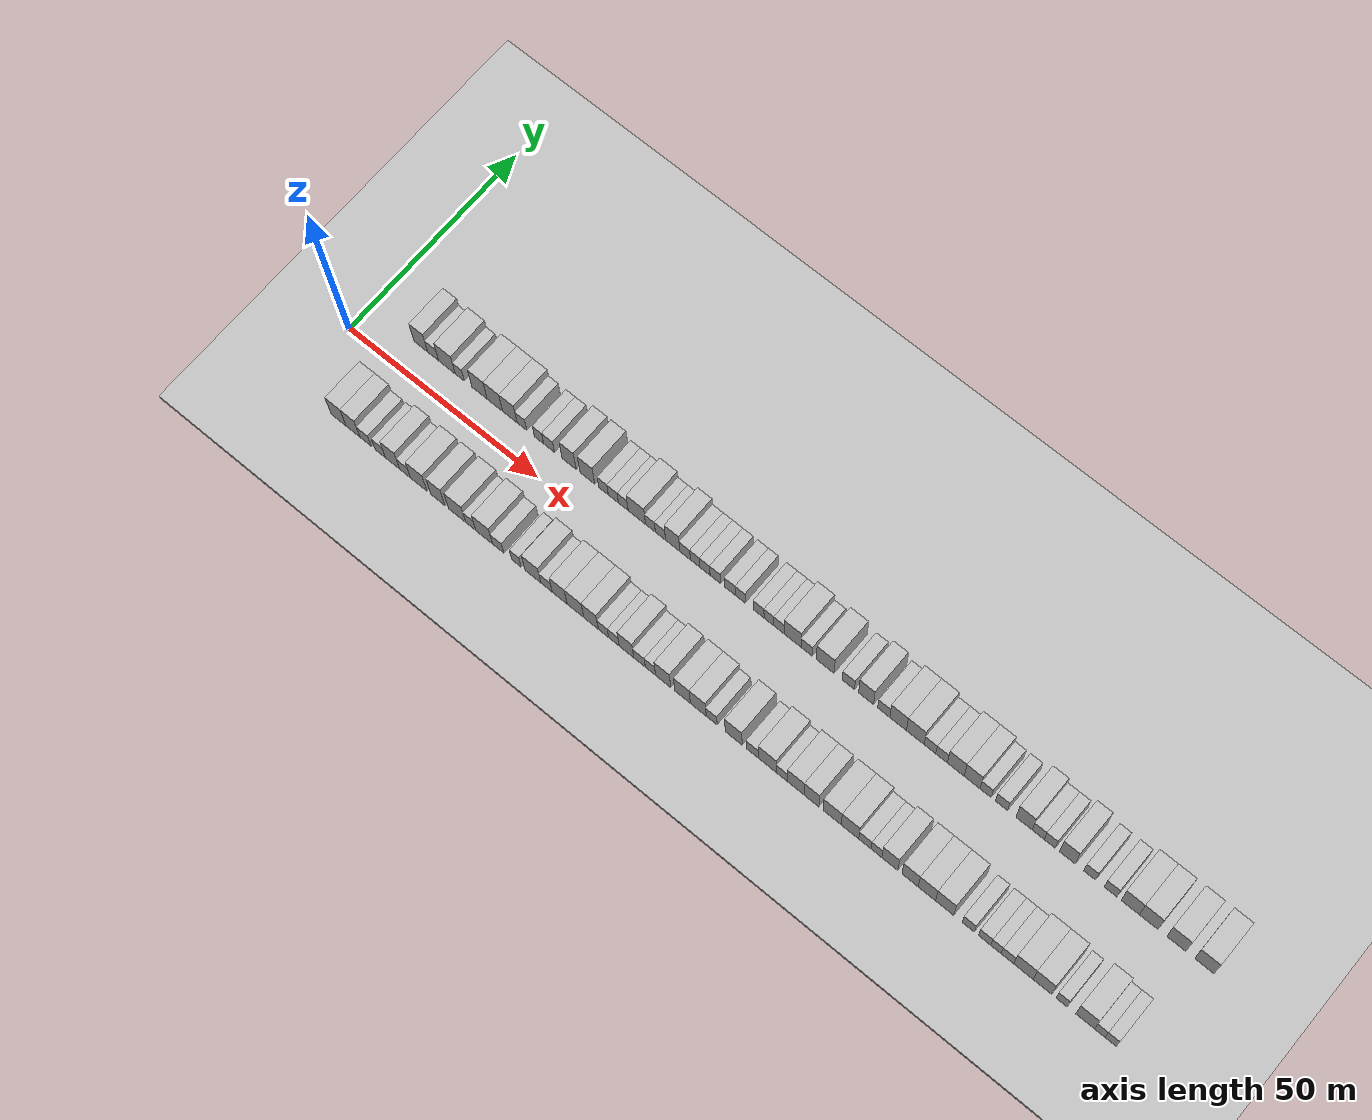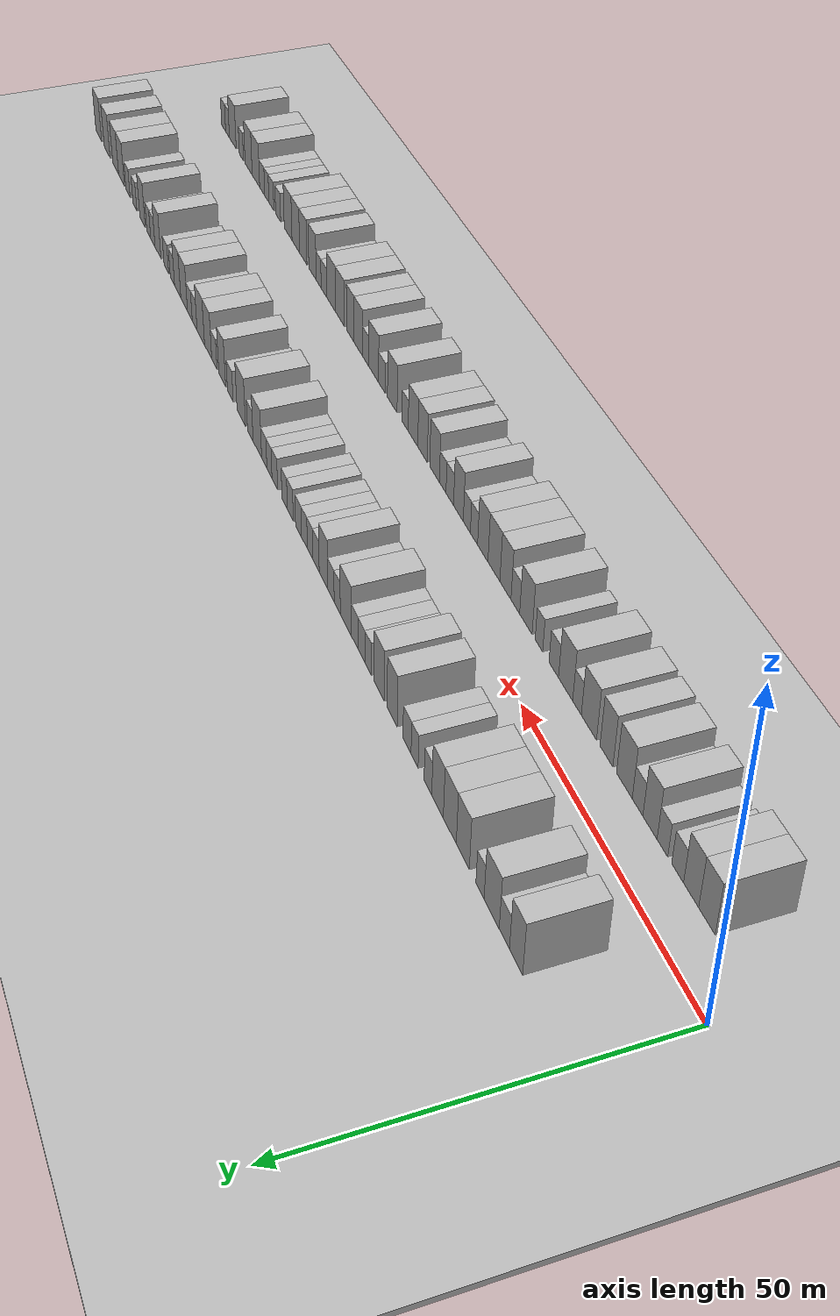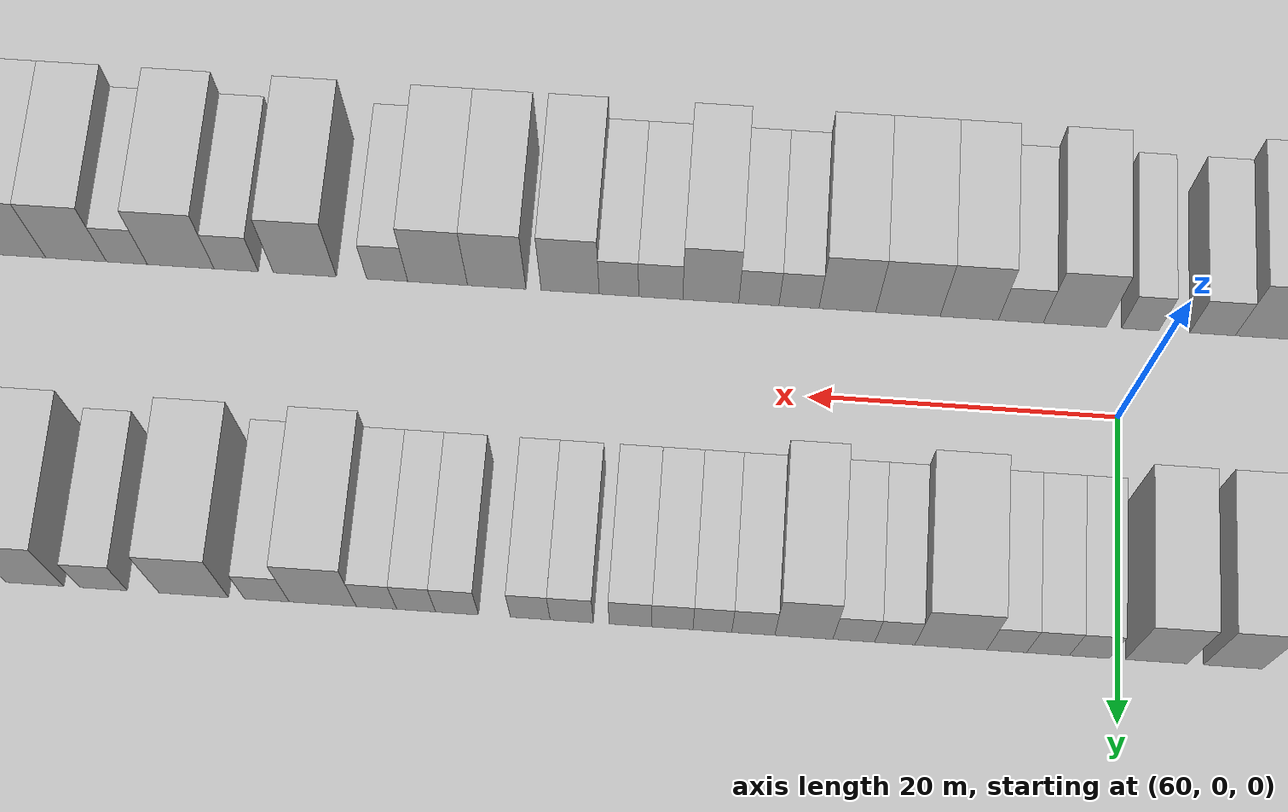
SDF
<?xml version="1.0" encoding="utf-8"?>

<sdf version="1.6">

   <world name="default">

      <gui fullscreen="0">

         <camera name="user_camera">

            <pose>-15 0 4.57585 0 0 0</pose>

            <view_controller>orbit</view_controller>

         </camera>

      </gui>

      <scene>

         <sky>

           <clouds>

             <speed>12</speed>

           </clouds>

         </sky>

         <ambient>0.4 0.4 0.4 1</ambient>

         <background>0.7 0.7 0.7 1</background>

         <shadows>1</shadows>

      </scene>

      <gravity>0 0 -9.8066</gravity>

      <magnetic_field>6e-06 2.3e-05 -4.2e-05</magnetic_field>

      <physics default="0" name="default_physics" type="ode">

         <ode>

            <solver>

               <type>quick</type>

               <iters>10</iters>

               <sor>1.0</sor>

               <use_dynamic_moi_rescaling>0</use_dynamic_moi_rescaling>

            </solver>

            <constraints>

               <cfm>0</cfm>

               <erp>0.2</erp>

               <contact_max_correcting_vel>100</contact_max_correcting_vel>

               <contact_surface_layer>0.001</contact_surface_layer>

            </constraints>

         </ode>

         <max_step_size>0.004</max_step_size>

         <real_time_factor>1</real_time_factor>

         <real_time_update_rate>250</real_time_update_rate>

      </physics>

      <light name="sun" type="directional">

         <cast_shadows>1</cast_shadows>

         <pose>0 0 10 0 0 0</pose>

         <diffuse>0.8 0.8 0.8 1</diffuse>

         <specular>0.2 0.2 0.2 1</specular>

         <attenuation>

            <range>1000</range>

            <constant>0.9</constant>

            <linear>0.01</linear>

            <quadratic>0.001</quadratic>

         </attenuation>

         <direction>-0.5 0.1 -0.9</direction>

      </light>

      <include>

         <name>ground_plane_1</name>

         <uri>model://HANNAS_ground_plane</uri>

         <pose>0 0 0  0 0 0</pose>

      </include>

      <include>

         <name>ground_plane_2</name>

         <uri>model://HANNAS_ground_plane</uri>

         <pose>100 0 0  0 0 0</pose>

      </include>

      <model name="building_1">

         <static>1</static>

         <pose frame="">13.8384 11.0000 0 0.000000 0.000000 1.570796</pose>

         <link name="link">

            <pose frame="">0 0 4.50 0 0 0</pose>

            <collision name="collision">

               <geometry>

                  <box>

                     <size>10.0000 3.6767 9.0000</size>

                  </box>

               </geometry>

               <max_contacts>10</max_contacts>

               <surface>

                  <contact>

                     <ode/>

                  </contact>

                  <bounce/>

                  <friction>

                     <torsional>

                        <ode/>

                     </torsional>

                     <ode/>

                  </friction>

               </surface>

            </collision>

            <visual name="visual">

               <cast_shadows>0</cast_shadows>

               <geometry>

                  <box>

                     <size>10.0000 3.6767 9.0000</size>

                  </box>

               </geometry>

               <material>

                  <script>

                     <uri>model://HANNAS_wall/materials/scripts</uri>

                     <uri>model://HANNAS_wall/materials/textures</uri>

                     <name>vrc/HANNAS_wall</name>

                  </script>

               </material>

            </visual>

            <self_collide>0</self_collide>

            <enable_wind>0</enable_wind>

            <kinematic>0</kinematic>

         </link>

      </model>

      <model name="building_2">

         <static>1</static>

         <pose frame="">17.1283 11.0000 0 0.000000 0.000000 1.570796</pose>

         <link name="link">

            <pose frame="">0 0 3.00 0 0 0</pose>

            <collision name="collision">

               <geometry>

                  <box>

                     <size>10.0000 2.9031 6.0000</size>

                  </box>

               </geometry>

               <max_contacts>10</max_contacts>

               <surface>

                  <contact>

                     <ode/>

                  </contact>

                  <bounce/>

                  <friction>

                     <torsional>

                        <ode/>

                     </torsional>

                     <ode/>

                  </friction>

               </surface>

            </collision>

            <visual name="visual">

               <cast_shadows>0</cast_shadows>

               <geometry>

                  <box>

                     <size>10.0000 2.9031 6.0000</size>

                  </box>

               </geometry>

               <material>

                  <script>

                     <uri>model://HANNAS_wall/materials/scripts</uri>

                     <uri>model://HANNAS_wall/materials/textures</uri>

                     <name>vrc/HANNAS_wall</name>

                  </script>

               </material>

            </visual>

            <self_collide>0</self_collide>

            <enable_wind>0</enable_wind>

            <kinematic>0</kinematic>

         </link>

      </model>

      <model name="building_3">

         <static>1</static>

         <pose frame="">20.7933 11.0000 0 0.000000 0.000000 1.570796</pose>

         <link name="link">

            <pose frame="">0 0 4.50 0 0 0</pose>

            <collision name="collision">

               <geometry>

                  <box>

                     <size>10.0000 4.4269 9.0000</size>

                  </box>

               </geometry>

               <max_contacts>10</max_contacts>

               <surface>

                  <contact>

                     <ode/>

                  </contact>

                  <bounce/>

                  <friction>

                     <torsional>

                        <ode/>

                     </torsional>

                     <ode/>

                  </friction>

               </surface>

            </collision>

            <visual name="visual">

               <cast_shadows>0</cast_shadows>

               <geometry>

                  <box>

                     <size>10.0000 4.4269 9.0000</size>

                  </box>

               </geometry>

               <material>

                  <script>

                     <uri>model://HANNAS_wall/materials/scripts</uri>

                     <uri>model://HANNAS_wall/materials/textures</uri>

                     <name>vrc/HANNAS_wall</name>

                  </script>

               </material>

            </visual>

            <self_collide>0</self_collide>

            <enable_wind>0</enable_wind>

            <kinematic>0</kinematic>

         </link>

      </model>

      <model name="building_4">

         <static>1</static>

         <pose frame="">24.2196 11.0000 0 0.000000 0.000000 1.570796</pose>

         <link name="link">

            <pose frame="">0 0 3.00 0 0 0</pose>

            <collision name="collision">

               <geometry>

                  <box>

                     <size>10.0000 2.4257 6.0000</size>

                  </box>

               </geometry>

               <max_contacts>10</max_contacts>

               <surface>

                  <contact>

                     <ode/>

                  </contact>

                  <bounce/>

                  <friction>

                     <torsional>

                        <ode/>

                     </torsional>

                     <ode/>

                  </friction>

               </surface>

            </collision>

            <visual name="visual">

               <cast_shadows>0</cast_shadows>

               <geometry>

                  <box>

                     <size>10.0000 2.4257 6.0000</size>

                  </box>

               </geometry>

               <material>

                  <script>

                     <uri>model://HANNAS_wall/materials/scripts</uri>

                     <uri>model://HANNAS_wall/materials/textures</uri>

                     <name>vrc/HANNAS_wall</name>

                  </script>

               </material>

            </visual>

            <self_collide>0</self_collide>

            <enable_wind>0</enable_wind>

            <kinematic>0</kinematic>

         </link>

      </model>

      <model name="building_5">

         <static>1</static>

         <pose frame="">29.4477 11.0000 0 0.000000 0.000000 1.570796</pose>

         <link name="link">

            <pose frame="">0 0 4.50 0 0 0</pose>

            <collision name="collision">

               <geometry>

                  <box>

                     <size>10.0000 4.0304 9.0000</size>

                  </box>

               </geometry>

               <max_contacts>10</max_contacts>

               <surface>

                  <contact>

                     <ode/>

                  </contact>

                  <bounce/>

                  <friction>

                     <torsional>

                        <ode/>

                     </torsional>

                     <ode/>

                  </friction>

               </surface>

            </collision>

            <visual name="visual">

               <cast_shadows>0</cast_shadows>

               <geometry>

                  <box>

                     <size>10.0000 4.0304 9.0000</size>

                  </box>

               </geometry>

               <material>

                  <script>

                     <uri>model://HANNAS_wall/materials/scripts</uri>

                     <uri>model://HANNAS_wall/materials/textures</uri>

                     <name>vrc/HANNAS_wall</name>

                  </script>

               </material>

            </visual>

            <self_collide>0</self_collide>

            <enable_wind>0</enable_wind>

            <kinematic>0</kinematic>

         </link>

      </model>

      <model name="building_6">

         <static>1</static>

         <pose frame="">33.5247 11.0000 0 0.000000 0.000000 1.570796</pose>

         <link name="link">

            <pose frame="">0 0 4.50 0 0 0</pose>

            <collision name="collision">

               <geometry>

                  <box>

                     <size>10.0000 4.1236 9.0000</size>

                  </box>

               </geometry>

               <max_contacts>10</max_contacts>

               <surface>

                  <contact>

                     <ode/>

                  </contact>

                  <bounce/>

                  <friction>

                     <torsional>

                        <ode/>

                     </torsional>

                     <ode/>

                  </friction>

               </surface>

            </collision>

            <visual name="visual">

               <cast_shadows>0</cast_shadows>

               <geometry>

                  <box>

                     <size>10.0000 4.1236 9.0000</size>

                  </box>

               </geometry>

               <material>

                  <script>

                     <uri>model://HANNAS_wall/materials/scripts</uri>

                     <uri>model://HANNAS_wall/materials/textures</uri>

                     <name>vrc/HANNAS_wall</name>

                  </script>

               </material>

            </visual>

            <self_collide>0</self_collide>

            <enable_wind>0</enable_wind>

            <kinematic>0</kinematic>

         </link>

      </model>

      <model name="building_7">

         <static>1</static>

         <pose frame="">37.4718 11.0000 0 0.000000 0.000000 1.570796</pose>

         <link name="link">

            <pose frame="">0 0 4.50 0 0 0</pose>

            <collision name="collision">

               <geometry>

                  <box>

                     <size>10.0000 3.7705 9.0000</size>

                  </box>

               </geometry>

               <max_contacts>10</max_contacts>

               <surface>

                  <contact>

                     <ode/>

                  </contact>

                  <bounce/>

                  <friction>

                     <torsional>

                        <ode/>

                     </torsional>

                     <ode/>

                  </friction>

               </surface>

            </collision>

            <visual name="visual">

               <cast_shadows>0</cast_shadows>

               <geometry>

                  <box>

                     <size>10.0000 3.7705 9.0000</size>

                  </box>

               </geometry>

               <material>

                  <script>

                     <uri>model://HANNAS_wall/materials/scripts</uri>

                     <uri>model://HANNAS_wall/materials/textures</uri>

                     <name>vrc/HANNAS_wall</name>

                  </script>

               </material>

            </visual>

            <self_collide>0</self_collide>

            <enable_wind>0</enable_wind>

            <kinematic>0</kinematic>

         </link>

      </model>

      <model name="building_8">

         <static>1</static>

         <pose frame="">40.6298 11.0000 0 0.000000 0.000000 1.570796</pose>

         <link name="link">

            <pose frame="">0 0 3.00 0 0 0</pose>

            <collision name="collision">

               <geometry>

                  <box>

                     <size>10.0000 2.5456 6.0000</size>

                  </box>

               </geometry>

               <max_contacts>10</max_contacts>

               <surface>

                  <contact>

                     <ode/>

                  </contact>

                  <bounce/>

                  <friction>

                     <torsional>

                        <ode/>

                     </torsional>

                     <ode/>

                  </friction>

               </surface>

            </collision>

            <visual name="visual">

               <cast_shadows>0</cast_shadows>

               <geometry>

                  <box>

                     <size>10.0000 2.5456 6.0000</size>

                  </box>

               </geometry>

               <material>

                  <script>

                     <uri>model://HANNAS_wall/materials/scripts</uri>

                     <uri>model://HANNAS_wall/materials/textures</uri>

                     <name>vrc/HANNAS_wall</name>

                  </script>

               </material>

            </visual>

            <self_collide>0</self_collide>

            <enable_wind>0</enable_wind>

            <kinematic>0</kinematic>

         </link>

      </model>

      <model name="building_9">

         <static>1</static>

         <pose frame="">45.1098 11.0000 0 0.000000 0.000000 1.570796</pose>

         <link name="link">

            <pose frame="">0 0 3.00 0 0 0</pose>

            <collision name="collision">

               <geometry>

                  <box>

                     <size>10.0000 2.4144 6.0000</size>

                  </box>

               </geometry>

               <max_contacts>10</max_contacts>

               <surface>

                  <contact>

                     <ode/>

                  </contact>

                  <bounce/>

                  <friction>

                     <torsional>

                        <ode/>

                     </torsional>

                     <ode/>

                  </friction>

               </surface>

            </collision>

            <visual name="visual">

               <cast_shadows>0</cast_shadows>

               <geometry>

                  <box>

                     <size>10.0000 2.4144 6.0000</size>

                  </box>

               </geometry>

               <material>

                  <script>

                     <uri>model://HANNAS_wall/materials/scripts</uri>

                     <uri>model://HANNAS_wall/materials/textures</uri>

                     <name>vrc/HANNAS_wall</name>

                  </script>

               </material>

            </visual>

            <self_collide>0</self_collide>

            <enable_wind>0</enable_wind>

            <kinematic>0</kinematic>

         </link>

      </model>

      <model name="building_10">

         <static>1</static>

         <pose frame="">47.7311 11.0000 0 0.000000 0.000000 1.570796</pose>

         <link name="link">

            <pose frame="">0 0 3.00 0 0 0</pose>

            <collision name="collision">

               <geometry>

                  <box>

                     <size>10.0000 2.8282 6.0000</size>

                  </box>

               </geometry>

               <max_contacts>10</max_contacts>

               <surface>

                  <contact>

                     <ode/>

                  </contact>

                  <bounce/>

                  <friction>

                     <torsional>

                        <ode/>

                     </torsional>

                     <ode/>

                  </friction>

               </surface>

            </collision>

            <visual name="visual">

               <cast_shadows>0</cast_shadows>

               <geometry>

                  <box>

                     <size>10.0000 2.8282 6.0000</size>

                  </box>

               </geometry>

               <material>

                  <script>

                     <uri>model://HANNAS_wall/materials/scripts</uri>

                     <uri>model://HANNAS_wall/materials/textures</uri>

                     <name>vrc/HANNAS_wall</name>

                  </script>

               </material>

            </visual>

            <self_collide>0</self_collide>

            <enable_wind>0</enable_wind>

            <kinematic>0</kinematic>

         </link>

      </model>

      <model name="building_11">

         <static>1</static>

         <pose frame="">52.9642 11.0000 0 0.000000 0.000000 1.570796</pose>

         <link name="link">

            <pose frame="">0 0 4.50 0 0 0</pose>

            <collision name="collision">

               <geometry>

                  <box>

                     <size>10.0000 3.6381 9.0000</size>

                  </box>

               </geometry>

               <max_contacts>10</max_contacts>

               <surface>

                  <contact>

                     <ode/>

                  </contact>

                  <bounce/>

                  <friction>

                     <torsional>

                        <ode/>

                     </torsional>

                     <ode/>

                  </friction>

               </surface>

            </collision>

            <visual name="visual">

               <cast_shadows>0</cast_shadows>

               <geometry>

                  <box>

                     <size>10.0000 3.6381 9.0000</size>

                  </box>

               </geometry>

               <material>

                  <script>

                     <uri>model://HANNAS_wall/materials/scripts</uri>

                     <uri>model://HANNAS_wall/materials/textures</uri>

                     <name>vrc/HANNAS_wall</name>

                  </script>

               </material>

            </visual>

            <self_collide>0</self_collide>

            <enable_wind>0</enable_wind>

            <kinematic>0</kinematic>

         </link>

      </model>

      <model name="building_12">

         <static>1</static>

         <pose frame="">57.6949 11.0000 0 0.000000 0.000000 1.570796</pose>

         <link name="link">

            <pose frame="">0 0 4.50 0 0 0</pose>

            <collision name="collision">

               <geometry>

                  <box>

                     <size>10.0000 3.8232 9.0000</size>

                  </box>

               </geometry>

               <max_contacts>10</max_contacts>

               <surface>

                  <contact>

                     <ode/>

                  </contact>

                  <bounce/>

                  <friction>

                     <torsional>

                        <ode/>

                     </torsional>

                     <ode/>

                  </friction>

               </surface>

            </collision>

            <visual name="visual">

               <cast_shadows>0</cast_shadows>

               <geometry>

                  <box>

                     <size>10.0000 3.8232 9.0000</size>

                  </box>

               </geometry>

               <material>

                  <script>

                     <uri>model://HANNAS_wall/materials/scripts</uri>

                     <uri>model://HANNAS_wall/materials/textures</uri>

                     <name>vrc/HANNAS_wall</name>

                  </script>

               </material>

            </visual>

            <self_collide>0</self_collide>

            <enable_wind>0</enable_wind>

            <kinematic>0</kinematic>

         </link>

      </model>

      <model name="building_13">

         <static>1</static>

         <pose frame="">61.8436 11.0000 0 0.000000 0.000000 1.570796</pose>

         <link name="link">

            <pose frame="">0 0 3.00 0 0 0</pose>

            <collision name="collision">

               <geometry>

                  <box>

                     <size>10.0000 2.4743 6.0000</size>

                  </box>

               </geometry>

               <max_contacts>10</max_contacts>

               <surface>

                  <contact>

                     <ode/>

                  </contact>

                  <bounce/>

                  <friction>

                     <torsional>

                        <ode/>

                     </torsional>

                     <ode/>

                  </friction>

               </surface>

            </collision>

            <visual name="visual">

               <cast_shadows>0</cast_shadows>

               <geometry>

                  <box>

                     <size>10.0000 2.4743 6.0000</size>

                  </box>

               </geometry>

               <material>

                  <script>

                     <uri>model://HANNAS_wall/materials/scripts</uri>

                     <uri>model://HANNAS_wall/materials/textures</uri>

                     <name>vrc/HANNAS_wall</name>

                  </script>

               </material>

            </visual>

            <self_collide>0</self_collide>

            <enable_wind>0</enable_wind>

            <kinematic>0</kinematic>

         </link>

      </model>

      <model name="building_14">

         <static>1</static>

         <pose frame="">64.3971 11.0000 0 0.000000 0.000000 1.570796</pose>

         <link name="link">

            <pose frame="">0 0 3.00 0 0 0</pose>

            <collision name="collision">

               <geometry>

                  <box>

                     <size>10.0000 2.6326 6.0000</size>

                  </box>

               </geometry>

               <max_contacts>10</max_contacts>

               <surface>

                  <contact>

                     <ode/>

                  </contact>

                  <bounce/>

                  <friction>

                     <torsional>

                        <ode/>

                     </torsional>

                     <ode/>

                  </friction>

               </surface>

            </collision>

            <visual name="visual">

               <cast_shadows>0</cast_shadows>

               <geometry>

                  <box>

                     <size>10.0000 2.6326 6.0000</size>

                  </box>

               </geometry>

               <material>

                  <script>

                     <uri>model://HANNAS_wall/materials/scripts</uri>

                     <uri>model://HANNAS_wall/materials/textures</uri>

                     <name>vrc/HANNAS_wall</name>

                  </script>

               </material>

            </visual>

            <self_collide>0</self_collide>

            <enable_wind>0</enable_wind>

            <kinematic>0</kinematic>

         </link>

      </model>

      <model name="building_15">

         <static>1</static>

         <pose frame="">66.9494 11.0000 0 0.000000 0.000000 1.570796</pose>

         <link name="link">

            <pose frame="">0 0 3.00 0 0 0</pose>

            <collision name="collision">

               <geometry>

                  <box>

                     <size>10.0000 2.4721 6.0000</size>

                  </box>

               </geometry>

               <max_contacts>10</max_contacts>

               <surface>

                  <contact>

                     <ode/>

                  </contact>

                  <bounce/>

                  <friction>

                     <torsional>

                        <ode/>

                     </torsional>

                     <ode/>

                  </friction>

               </surface>

            </collision>

            <visual name="visual">

               <cast_shadows>0</cast_shadows>

               <geometry>

                  <box>

                     <size>10.0000 2.4721 6.0000</size>

                  </box>

               </geometry>

               <material>

                  <script>

                     <uri>model://HANNAS_wall/materials/scripts</uri>

                     <uri>model://HANNAS_wall/materials/textures</uri>

                     <name>vrc/HANNAS_wall</name>

                  </script>

               </material>

            </visual>

            <self_collide>0</self_collide>

            <enable_wind>0</enable_wind>

            <kinematic>0</kinematic>

         </link>

      </model>

      <model name="building_16">

         <static>1</static>

         <pose frame="">70.4170 11.0000 0 0.000000 0.000000 1.570796</pose>

         <link name="link">

            <pose frame="">0 0 4.50 0 0 0</pose>

            <collision name="collision">

               <geometry>

                  <box>

                     <size>10.0000 4.4631 9.0000</size>

                  </box>

               </geometry>

               <max_contacts>10</max_contacts>

               <surface>

                  <contact>

                     <ode/>

                  </contact>

                  <bounce/>

                  <friction>

                     <torsional>

                        <ode/>

                     </torsional>

                     <ode/>

                  </friction>

               </surface>

            </collision>

            <visual name="visual">

               <cast_shadows>0</cast_shadows>

               <geometry>

                  <box>

                     <size>10.0000 4.4631 9.0000</size>

                  </box>

               </geometry>

               <material>

                  <script>

                     <uri>model://HANNAS_wall/materials/scripts</uri>

                     <uri>model://HANNAS_wall/materials/textures</uri>

                     <name>vrc/HANNAS_wall</name>

                  </script>

               </material>

            </visual>

            <self_collide>0</self_collide>

            <enable_wind>0</enable_wind>

            <kinematic>0</kinematic>

         </link>

      </model>

      <model name="building_17">

         <static>1</static>

         <pose frame="">73.8974 11.0000 0 0.000000 0.000000 1.570796</pose>

         <link name="link">

            <pose frame="">0 0 3.00 0 0 0</pose>

            <collision name="collision">

               <geometry>

                  <box>

                     <size>10.0000 2.4979 6.0000</size>

                  </box>

               </geometry>

               <max_contacts>10</max_contacts>

               <surface>

                  <contact>

                     <ode/>

                  </contact>

                  <bounce/>

                  <friction>

                     <torsional>

                        <ode/>

                     </torsional>

                     <ode/>

                  </friction>

               </surface>

            </collision>

            <visual name="visual">

               <cast_shadows>0</cast_shadows>

               <geometry>

                  <box>

                     <size>10.0000 2.4979 6.0000</size>

                  </box>

               </geometry>

               <material>

                  <script>

                     <uri>model://HANNAS_wall/materials/scripts</uri>

                     <uri>model://HANNAS_wall/materials/textures</uri>

                     <name>vrc/HANNAS_wall</name>

                  </script>

               </material>

            </visual>

            <self_collide>0</self_collide>

            <enable_wind>0</enable_wind>

            <kinematic>0</kinematic>

         </link>

      </model>

      <model name="building_18">

         <static>1</static>

         <pose frame="">76.4460 11.0000 0 0.000000 0.000000 1.570796</pose>

         <link name="link">

            <pose frame="">0 0 3.00 0 0 0</pose>

            <collision name="collision">

               <geometry>

                  <box>

                     <size>10.0000 2.5992 6.0000</size>

                  </box>

               </geometry>

               <max_contacts>10</max_contacts>

               <surface>

                  <contact>

                     <ode/>

                  </contact>

                  <bounce/>

                  <friction>

                     <torsional>

                        <ode/>

                     </torsional>

                     <ode/>

                  </friction>

               </surface>

            </collision>

            <visual name="visual">

               <cast_shadows>0</cast_shadows>

               <geometry>

                  <box>

                     <size>10.0000 2.5992 6.0000</size>

                  </box>

               </geometry>

               <material>

                  <script>

                     <uri>model://HANNAS_wall/materials/scripts</uri>

                     <uri>model://HANNAS_wall/materials/textures</uri>

                     <name>vrc/HANNAS_wall</name>

                  </script>

               </material>

            </visual>

            <self_collide>0</self_collide>

            <enable_wind>0</enable_wind>

            <kinematic>0</kinematic>

         </link>

      </model>

      <model name="building_19">

         <static>1</static>

         <pose frame="">79.5519 11.0000 0 0.000000 0.000000 1.570796</pose>

         <link name="link">

            <pose frame="">0 0 4.50 0 0 0</pose>

            <collision name="collision">

               <geometry>

                  <box>

                     <size>10.0000 3.6126 9.0000</size>

                  </box>

               </geometry>

               <max_contacts>10</max_contacts>

               <surface>

                  <contact>

                     <ode/>

                  </contact>

                  <bounce/>

                  <friction>

                     <torsional>

                        <ode/>

                     </torsional>

                     <ode/>

                  </friction>

               </surface>

            </collision>

            <visual name="visual">

               <cast_shadows>0</cast_shadows>

               <geometry>

                  <box>

                     <size>10.0000 3.6126 9.0000</size>

                  </box>

               </geometry>

               <material>

                  <script>

                     <uri>model://HANNAS_wall/materials/scripts</uri>

                     <uri>model://HANNAS_wall/materials/textures</uri>

                     <name>vrc/HANNAS_wall</name>

                  </script>

               </material>

            </visual>

            <self_collide>0</self_collide>

            <enable_wind>0</enable_wind>

            <kinematic>0</kinematic>

         </link>

      </model>

      <model name="building_20">

         <static>1</static>

         <pose frame="">82.6982 11.0000 0 0.000000 0.000000 1.570796</pose>

         <link name="link">

            <pose frame="">0 0 3.00 0 0 0</pose>

            <collision name="collision">

               <geometry>

                  <box>

                     <size>10.0000 2.6799 6.0000</size>

                  </box>

               </geometry>

               <max_contacts>10</max_contacts>

               <surface>

                  <contact>

                     <ode/>

                  </contact>

                  <bounce/>

                  <friction>

                     <torsional>

                        <ode/>

                     </torsional>

                     <ode/>

                  </friction>

               </surface>

            </collision>

            <visual name="visual">

               <cast_shadows>0</cast_shadows>

               <geometry>

                  <box>

                     <size>10.0000 2.6799 6.0000</size>

                  </box>

               </geometry>

               <material>

                  <script>

                     <uri>model://HANNAS_wall/materials/scripts</uri>

                     <uri>model://HANNAS_wall/materials/textures</uri>

                     <name>vrc/HANNAS_wall</name>

                  </script>

               </material>

            </visual>

            <self_collide>0</self_collide>

            <enable_wind>0</enable_wind>

            <kinematic>0</kinematic>

         </link>

      </model>

      <model name="building_21">

         <static>1</static>

         <pose frame="">85.2467 11.0000 0 0.000000 0.000000 1.570796</pose>

         <link name="link">

            <pose frame="">0 0 3.00 0 0 0</pose>

            <collision name="collision">

               <geometry>

                  <box>

                     <size>10.0000 2.4171 6.0000</size>

                  </box>

               </geometry>

               <max_contacts>10</max_contacts>

               <surface>

                  <contact>

                     <ode/>

                  </contact>

                  <bounce/>

                  <friction>

                     <torsional>

                        <ode/>

                     </torsional>

                     <ode/>

                  </friction>

               </surface>

            </collision>

            <visual name="visual">

               <cast_shadows>0</cast_shadows>

               <geometry>

                  <box>

                     <size>10.0000 2.4171 6.0000</size>

                  </box>

               </geometry>

               <material>

                  <script>

                     <uri>model://HANNAS_wall/materials/scripts</uri>

                     <uri>model://HANNAS_wall/materials/textures</uri>

                     <name>vrc/HANNAS_wall</name>

                  </script>

               </material>

            </visual>

            <self_collide>0</self_collide>

            <enable_wind>0</enable_wind>

            <kinematic>0</kinematic>

         </link>

      </model>

      <model name="building_22">

         <static>1</static>

         <pose frame="">87.7346 11.0000 0 0.000000 0.000000 1.570796</pose>

         <link name="link">

            <pose frame="">0 0 3.00 0 0 0</pose>

            <collision name="collision">

               <geometry>

                  <box>

                     <size>10.0000 2.5588 6.0000</size>

                  </box>

               </geometry>

               <max_contacts>10</max_contacts>

               <surface>

                  <contact>

                     <ode/>

                  </contact>

                  <bounce/>

                  <friction>

                     <torsional>

                        <ode/>

                     </torsional>

                     <ode/>

                  </friction>

               </surface>

            </collision>

            <visual name="visual">

               <cast_shadows>0</cast_shadows>

               <geometry>

                  <box>

                     <size>10.0000 2.5588 6.0000</size>

                  </box>

               </geometry>

               <material>

                  <script>

                     <uri>model://HANNAS_wall/materials/scripts</uri>

                     <uri>model://HANNAS_wall/materials/textures</uri>

                     <name>vrc/HANNAS_wall</name>

                  </script>

               </material>

            </visual>

            <self_collide>0</self_collide>

            <enable_wind>0</enable_wind>

            <kinematic>0</kinematic>

         </link>

      </model>

      <model name="building_23">

         <static>1</static>

         <pose frame="">90.3410 11.0000 0 0.000000 0.000000 1.570796</pose>

         <link name="link">

            <pose frame="">0 0 3.00 0 0 0</pose>

            <collision name="collision">

               <geometry>

                  <box>

                     <size>10.0000 2.6539 6.0000</size>

                  </box>

               </geometry>

               <max_contacts>10</max_contacts>

               <surface>

                  <contact>

                     <ode/>

                  </contact>

                  <bounce/>

                  <friction>

                     <torsional>

                        <ode/>

                     </torsional>

                     <ode/>

                  </friction>

               </surface>

            </collision>

            <visual name="visual">

               <cast_shadows>0</cast_shadows>

               <geometry>

                  <box>

                     <size>10.0000 2.6539 6.0000</size>

                  </box>

               </geometry>

               <material>

                  <script>

                     <uri>model://HANNAS_wall/materials/scripts</uri>

                     <uri>model://HANNAS_wall/materials/textures</uri>

                     <name>vrc/HANNAS_wall</name>

                  </script>

               </material>

            </visual>

            <self_collide>0</self_collide>

            <enable_wind>0</enable_wind>

            <kinematic>0</kinematic>

         </link>

      </model>

      <model name="building_24">

         <static>1</static>

         <pose frame="">94.0179 11.0000 0 0.000000 0.000000 1.570796</pose>

         <link name="link">

            <pose frame="">0 0 3.00 0 0 0</pose>

            <collision name="collision">

               <geometry>

                  <box>

                     <size>10.0000 2.7001 6.0000</size>

                  </box>

               </geometry>

               <max_contacts>10</max_contacts>

               <surface>

                  <contact>

                     <ode/>

                  </contact>

                  <bounce/>

                  <friction>

                     <torsional>

                        <ode/>

                     </torsional>

                     <ode/>

                  </friction>

               </surface>

            </collision>

            <visual name="visual">

               <cast_shadows>0</cast_shadows>

               <geometry>

                  <box>

                     <size>10.0000 2.7001 6.0000</size>

                  </box>

               </geometry>

               <material>

                  <script>

                     <uri>model://HANNAS_wall/materials/scripts</uri>

                     <uri>model://HANNAS_wall/materials/textures</uri>

                     <name>vrc/HANNAS_wall</name>

                  </script>

               </material>

            </visual>

            <self_collide>0</self_collide>

            <enable_wind>0</enable_wind>

            <kinematic>0</kinematic>

         </link>

      </model>

      <model name="building_25">

         <static>1</static>

         <pose frame="">96.6080 11.0000 0 0.000000 0.000000 1.570796</pose>

         <link name="link">

            <pose frame="">0 0 3.00 0 0 0</pose>

            <collision name="collision">

               <geometry>

                  <box>

                     <size>10.0000 2.4800 6.0000</size>

                  </box>

               </geometry>

               <max_contacts>10</max_contacts>

               <surface>

                  <contact>

                     <ode/>

                  </contact>

                  <bounce/>

                  <friction>

                     <torsional>

                        <ode/>

                     </torsional>

                     <ode/>

                  </friction>

               </surface>

            </collision>

            <visual name="visual">

               <cast_shadows>0</cast_shadows>

               <geometry>

                  <box>

                     <size>10.0000 2.4800 6.0000</size>

                  </box>

               </geometry>

               <material>

                  <script>

                     <uri>model://HANNAS_wall/materials/scripts</uri>

                     <uri>model://HANNAS_wall/materials/textures</uri>

                     <name>vrc/HANNAS_wall</name>

                  </script>

               </material>

            </visual>

            <self_collide>0</self_collide>

            <enable_wind>0</enable_wind>

            <kinematic>0</kinematic>

         </link>

      </model>

      <model name="building_26">

         <static>1</static>

         <pose frame="">101.1926 11.0000 0 0.000000 0.000000 1.570796</pose>

         <link name="link">

            <pose frame="">0 0 3.00 0 0 0</pose>

            <collision name="collision">

               <geometry>

                  <box>

                     <size>10.0000 2.6893 6.0000</size>

                  </box>

               </geometry>

               <max_contacts>10</max_contacts>

               <surface>

                  <contact>

                     <ode/>

                  </contact>

                  <bounce/>

                  <friction>

                     <torsional>

                        <ode/>

                     </torsional>

                     <ode/>

                  </friction>

               </surface>

            </collision>

            <visual name="visual">

               <cast_shadows>0</cast_shadows>

               <geometry>

                  <box>

                     <size>10.0000 2.6893 6.0000</size>

                  </box>

               </geometry>

               <material>

                  <script>

                     <uri>model://HANNAS_wall/materials/scripts</uri>

                     <uri>model://HANNAS_wall/materials/textures</uri>

                     <name>vrc/HANNAS_wall</name>

                  </script>

               </material>

            </visual>

            <self_collide>0</self_collide>

            <enable_wind>0</enable_wind>

            <kinematic>0</kinematic>

         </link>

      </model>

      <model name="building_27">

         <static>1</static>

         <pose frame="">103.7505 11.0000 0 0.000000 0.000000 1.570796</pose>

         <link name="link">

            <pose frame="">0 0 3.00 0 0 0</pose>

            <collision name="collision">

               <geometry>

                  <box>

                     <size>10.0000 2.4264 6.0000</size>

                  </box>

               </geometry>

               <max_contacts>10</max_contacts>

               <surface>

                  <contact>

                     <ode/>

                  </contact>

                  <bounce/>

                  <friction>

                     <torsional>

                        <ode/>

                     </torsional>

                     <ode/>

                  </friction>

               </surface>

            </collision>

            <visual name="visual">

               <cast_shadows>0</cast_shadows>

               <geometry>

                  <box>

                     <size>10.0000 2.4264 6.0000</size>

                  </box>

               </geometry>

               <material>

                  <script>

                     <uri>model://HANNAS_wall/materials/scripts</uri>

                     <uri>model://HANNAS_wall/materials/textures</uri>

                     <name>vrc/HANNAS_wall</name>

                  </script>

               </material>

            </visual>

            <self_collide>0</self_collide>

            <enable_wind>0</enable_wind>

            <kinematic>0</kinematic>

         </link>

      </model>

      <model name="building_28">

         <static>1</static>

         <pose frame="">106.2379 11.0000 0 0.000000 0.000000 1.570796</pose>

         <link name="link">

            <pose frame="">0 0 3.00 0 0 0</pose>

            <collision name="collision">

               <geometry>

                  <box>

                     <size>10.0000 2.5483 6.0000</size>

                  </box>

               </geometry>

               <max_contacts>10</max_contacts>

               <surface>

                  <contact>

                     <ode/>

                  </contact>

                  <bounce/>

                  <friction>

                     <torsional>

                        <ode/>

                     </torsional>

                     <ode/>

                  </friction>

               </surface>

            </collision>

            <visual name="visual">

               <cast_shadows>0</cast_shadows>

               <geometry>

                  <box>

                     <size>10.0000 2.5483 6.0000</size>

                  </box>

               </geometry>

               <material>

                  <script>

                     <uri>model://HANNAS_wall/materials/scripts</uri>

                     <uri>model://HANNAS_wall/materials/textures</uri>

                     <name>vrc/HANNAS_wall</name>

                  </script>

               </material>

            </visual>

            <self_collide>0</self_collide>

            <enable_wind>0</enable_wind>

            <kinematic>0</kinematic>

         </link>

      </model>

      <model name="building_29">

         <static>1</static>

         <pose frame="">109.6192 11.0000 0 0.000000 0.000000 1.570796</pose>

         <link name="link">

            <pose frame="">0 0 4.50 0 0 0</pose>

            <collision name="collision">

               <geometry>

                  <box>

                     <size>10.0000 4.2144 9.0000</size>

                  </box>

               </geometry>

               <max_contacts>10</max_contacts>

               <surface>

                  <contact>

                     <ode/>

                  </contact>

                  <bounce/>

                  <friction>

                     <torsional>

                        <ode/>

                     </torsional>

                     <ode/>

                  </friction>

               </surface>

            </collision>

            <visual name="visual">

               <cast_shadows>0</cast_shadows>

               <geometry>

                  <box>

                     <size>10.0000 4.2144 9.0000</size>

                  </box>

               </geometry>

               <material>

                  <script>

                     <uri>model://HANNAS_wall/materials/scripts</uri>

                     <uri>model://HANNAS_wall/materials/textures</uri>

                     <name>vrc/HANNAS_wall</name>

                  </script>

               </material>

            </visual>

            <self_collide>0</self_collide>

            <enable_wind>0</enable_wind>

            <kinematic>0</kinematic>

         </link>

      </model>

      <model name="building_30">

         <static>1</static>

         <pose frame="">113.1307 11.0000 0 0.000000 0.000000 1.570796</pose>

         <link name="link">

            <pose frame="">0 0 3.00 0 0 0</pose>

            <collision name="collision">

               <geometry>

                  <box>

                     <size>10.0000 2.8086 6.0000</size>

                  </box>

               </geometry>

               <max_contacts>10</max_contacts>

               <surface>

                  <contact>

                     <ode/>

                  </contact>

                  <bounce/>

                  <friction>

                     <torsional>

                        <ode/>

                     </torsional>

                     <ode/>

                  </friction>

               </surface>

            </collision>

            <visual name="visual">

               <cast_shadows>0</cast_shadows>

               <geometry>

                  <box>

                     <size>10.0000 2.8086 6.0000</size>

                  </box>

               </geometry>

               <material>

                  <script>

                     <uri>model://HANNAS_wall/materials/scripts</uri>

                     <uri>model://HANNAS_wall/materials/textures</uri>

                     <name>vrc/HANNAS_wall</name>

                  </script>

               </material>

            </visual>

            <self_collide>0</self_collide>

            <enable_wind>0</enable_wind>

            <kinematic>0</kinematic>

         </link>

      </model>

      <model name="building_31">

         <static>1</static>

         <pose frame="">117.7258 11.0000 0 0.000000 0.000000 1.570796</pose>

         <link name="link">

            <pose frame="">0 0 4.50 0 0 0</pose>

            <collision name="collision">

               <geometry>

                  <box>

                     <size>10.0000 4.3816 9.0000</size>

                  </box>

               </geometry>

               <max_contacts>10</max_contacts>

               <surface>

                  <contact>

                     <ode/>

                  </contact>

                  <bounce/>

                  <friction>

                     <torsional>

                        <ode/>

                     </torsional>

                     <ode/>

                  </friction>

               </surface>

            </collision>

            <visual name="visual">

               <cast_shadows>0</cast_shadows>

               <geometry>

                  <box>

                     <size>10.0000 4.3816 9.0000</size>

                  </box>

               </geometry>

               <material>

                  <script>

                     <uri>model://HANNAS_wall/materials/scripts</uri>

                     <uri>model://HANNAS_wall/materials/textures</uri>

                     <name>vrc/HANNAS_wall</name>

                  </script>

               </material>

            </visual>

            <self_collide>0</self_collide>

            <enable_wind>0</enable_wind>

            <kinematic>0</kinematic>

         </link>

      </model>

      <model name="building_32">

         <static>1</static>

         <pose frame="">123.4141 11.0000 0 0.000000 0.000000 1.570796</pose>

         <link name="link">

            <pose frame="">0 0 3.00 0 0 0</pose>

            <collision name="collision">

               <geometry>

                  <box>

                     <size>10.0000 2.9950 6.0000</size>

                  </box>

               </geometry>

               <max_contacts>10</max_contacts>

               <surface>

                  <contact>

                     <ode/>

                  </contact>

                  <bounce/>

                  <friction>

                     <torsional>

                        <ode/>

                     </torsional>

                     <ode/>

                  </friction>

               </surface>

            </collision>

            <visual name="visual">

               <cast_shadows>0</cast_shadows>

               <geometry>

                  <box>

                     <size>10.0000 2.9950 6.0000</size>

                  </box>

               </geometry>

               <material>

                  <script>

                     <uri>model://HANNAS_wall/materials/scripts</uri>

                     <uri>model://HANNAS_wall/materials/textures</uri>

                     <name>vrc/HANNAS_wall</name>

                  </script>

               </material>

            </visual>

            <self_collide>0</self_collide>

            <enable_wind>0</enable_wind>

            <kinematic>0</kinematic>

         </link>

      </model>

      <model name="building_33">

         <static>1</static>

         <pose frame="">127.7381 11.0000 0 0.000000 0.000000 1.570796</pose>

         <link name="link">

            <pose frame="">0 0 4.50 0 0 0</pose>

            <collision name="collision">

               <geometry>

                  <box>

                     <size>10.0000 3.6529 9.0000</size>

                  </box>

               </geometry>

               <max_contacts>10</max_contacts>

               <surface>

                  <contact>

                     <ode/>

                  </contact>

                  <bounce/>

                  <friction>

                     <torsional>

                        <ode/>

                     </torsional>

                     <ode/>

                  </friction>

               </surface>

            </collision>

            <visual name="visual">

               <cast_shadows>0</cast_shadows>

               <geometry>

                  <box>

                     <size>10.0000 3.6529 9.0000</size>

                  </box>

               </geometry>

               <material>

                  <script>

                     <uri>model://HANNAS_wall/materials/scripts</uri>

                     <uri>model://HANNAS_wall/materials/textures</uri>

                     <name>vrc/HANNAS_wall</name>

                  </script>

               </material>

            </visual>

            <self_collide>0</self_collide>

            <enable_wind>0</enable_wind>

            <kinematic>0</kinematic>

         </link>

      </model>

      <model name="building_34">

         <static>1</static>

         <pose frame="">132.0323 11.0000 0 0.000000 0.000000 1.570796</pose>

         <link name="link">

            <pose frame="">0 0 3.00 0 0 0</pose>

            <collision name="collision">

               <geometry>

                  <box>

                     <size>10.0000 2.9356 6.0000</size>

                  </box>

               </geometry>

               <max_contacts>10</max_contacts>

               <surface>

                  <contact>

                     <ode/>

                  </contact>

                  <bounce/>

                  <friction>

                     <torsional>

                        <ode/>

                     </torsional>

                     <ode/>

                  </friction>

               </surface>

            </collision>

            <visual name="visual">

               <cast_shadows>0</cast_shadows>

               <geometry>

                  <box>

                     <size>10.0000 2.9356 6.0000</size>

                  </box>

               </geometry>

               <material>

                  <script>

                     <uri>model://HANNAS_wall/materials/scripts</uri>

                     <uri>model://HANNAS_wall/materials/textures</uri>

                     <name>vrc/HANNAS_wall</name>

                  </script>

               </material>

            </visual>

            <self_collide>0</self_collide>

            <enable_wind>0</enable_wind>

            <kinematic>0</kinematic>

         </link>

      </model>

      <model name="building_35">

         <static>1</static>

         <pose frame="">135.5147 11.0000 0 0.000000 0.000000 1.570796</pose>

         <link name="link">

            <pose frame="">0 0 4.50 0 0 0</pose>

            <collision name="collision">

               <geometry>

                  <box>

                     <size>10.0000 4.0293 9.0000</size>

                  </box>

               </geometry>

               <max_contacts>10</max_contacts>

               <surface>

                  <contact>

                     <ode/>

                  </contact>

                  <bounce/>

                  <friction>

                     <torsional>

                        <ode/>

                     </torsional>

                     <ode/>

                  </friction>

               </surface>

            </collision>

            <visual name="visual">

               <cast_shadows>0</cast_shadows>

               <geometry>

                  <box>

                     <size>10.0000 4.0293 9.0000</size>

                  </box>

               </geometry>

               <material>

                  <script>

                     <uri>model://HANNAS_wall/materials/scripts</uri>

                     <uri>model://HANNAS_wall/materials/textures</uri>

                     <name>vrc/HANNAS_wall</name>

                  </script>

               </material>

            </visual>

            <self_collide>0</self_collide>

            <enable_wind>0</enable_wind>

            <kinematic>0</kinematic>

         </link>

      </model>

      <model name="building_36">

         <static>1</static>

         <pose frame="">139.6700 11.0000 0 0.000000 0.000000 1.570796</pose>

         <link name="link">

            <pose frame="">0 0 4.50 0 0 0</pose>

            <collision name="collision">

               <geometry>

                  <box>

                     <size>10.0000 4.2813 9.0000</size>

                  </box>

               </geometry>

               <max_contacts>10</max_contacts>

               <surface>

                  <contact>

                     <ode/>

                  </contact>

                  <bounce/>

                  <friction>

                     <torsional>

                        <ode/>

                     </torsional>

                     <ode/>

                  </friction>

               </surface>

            </collision>

            <visual name="visual">

               <cast_shadows>0</cast_shadows>

               <geometry>

                  <box>

                     <size>10.0000 4.2813 9.0000</size>

                  </box>

               </geometry>

               <material>

                  <script>

                     <uri>model://HANNAS_wall/materials/scripts</uri>

                     <uri>model://HANNAS_wall/materials/textures</uri>

                     <name>vrc/HANNAS_wall</name>

                  </script>

               </material>

            </visual>

            <self_collide>0</self_collide>

            <enable_wind>0</enable_wind>

            <kinematic>0</kinematic>

         </link>

      </model>

      <model name="building_37">

         <static>1</static>

         <pose frame="">143.2204 11.0000 0 0.000000 0.000000 1.570796</pose>

         <link name="link">

            <pose frame="">0 0 3.00 0 0 0</pose>

            <collision name="collision">

               <geometry>

                  <box>

                     <size>10.0000 2.8195 6.0000</size>

                  </box>

               </geometry>

               <max_contacts>10</max_contacts>

               <surface>

                  <contact>

                     <ode/>

                  </contact>

                  <bounce/>

                  <friction>

                     <torsional>

                        <ode/>

                     </torsional>

                     <ode/>

                  </friction>

               </surface>

            </collision>

            <visual name="visual">

               <cast_shadows>0</cast_shadows>

               <geometry>

                  <box>

                     <size>10.0000 2.8195 6.0000</size>

                  </box>

               </geometry>

               <material>

                  <script>

                     <uri>model://HANNAS_wall/materials/scripts</uri>

                     <uri>model://HANNAS_wall/materials/textures</uri>

                     <name>vrc/HANNAS_wall</name>

                  </script>

               </material>

            </visual>

            <self_collide>0</self_collide>

            <enable_wind>0</enable_wind>

            <kinematic>0</kinematic>

         </link>

      </model>

      <model name="building_38">

         <static>1</static>

         <pose frame="">146.0346 11.0000 0 0.000000 0.000000 1.570796</pose>

         <link name="link">

            <pose frame="">0 0 3.00 0 0 0</pose>

            <collision name="collision">

               <geometry>

                  <box>

                     <size>10.0000 2.8088 6.0000</size>

                  </box>

               </geometry>

               <max_contacts>10</max_contacts>

               <surface>

                  <contact>

                     <ode/>

                  </contact>

                  <bounce/>

                  <friction>

                     <torsional>

                        <ode/>

                     </torsional>

                     <ode/>

                  </friction>

               </surface>

            </collision>

            <visual name="visual">

               <cast_shadows>0</cast_shadows>

               <geometry>

                  <box>

                     <size>10.0000 2.8088 6.0000</size>

                  </box>

               </geometry>

               <material>

                  <script>

                     <uri>model://HANNAS_wall/materials/scripts</uri>

                     <uri>model://HANNAS_wall/materials/textures</uri>

                     <name>vrc/HANNAS_wall</name>

                  </script>

               </material>

            </visual>

            <self_collide>0</self_collide>

            <enable_wind>0</enable_wind>

            <kinematic>0</kinematic>

         </link>

      </model>

      <model name="building_39">

         <static>1</static>

         <pose frame="">149.4398 11.0000 0 0.000000 0.000000 1.570796</pose>

         <link name="link">

            <pose frame="">0 0 4.50 0 0 0</pose>

            <collision name="collision">

               <geometry>

                  <box>

                     <size>10.0000 4.0015 9.0000</size>

                  </box>

               </geometry>

               <max_contacts>10</max_contacts>

               <surface>

                  <contact>

                     <ode/>

                  </contact>

                  <bounce/>

                  <friction>

                     <torsional>

                        <ode/>

                     </torsional>

                     <ode/>

                  </friction>

               </surface>

            </collision>

            <visual name="visual">

               <cast_shadows>0</cast_shadows>

               <geometry>

                  <box>

                     <size>10.0000 4.0015 9.0000</size>

                  </box>

               </geometry>

               <material>

                  <script>

                     <uri>model://HANNAS_wall/materials/scripts</uri>

                     <uri>model://HANNAS_wall/materials/textures</uri>

                     <name>vrc/HANNAS_wall</name>

                  </script>

               </material>

            </visual>

            <self_collide>0</self_collide>

            <enable_wind>0</enable_wind>

            <kinematic>0</kinematic>

         </link>

      </model>

      <model name="building_40">

         <static>1</static>

         <pose frame="">153.3463 11.0000 0 0.000000 0.000000 1.570796</pose>

         <link name="link">

            <pose frame="">0 0 4.50 0 0 0</pose>

            <collision name="collision">

               <geometry>

                  <box>

                     <size>10.0000 3.8114 9.0000</size>

                  </box>

               </geometry>

               <max_contacts>10</max_contacts>

               <surface>

                  <contact>

                     <ode/>

                  </contact>

                  <bounce/>

                  <friction>

                     <torsional>

                        <ode/>

                     </torsional>

                     <ode/>

                  </friction>

               </surface>

            </collision>

            <visual name="visual">

               <cast_shadows>0</cast_shadows>

               <geometry>

                  <box>

                     <size>10.0000 3.8114 9.0000</size>

                  </box>

               </geometry>

               <material>

                  <script>

                     <uri>model://HANNAS_wall/materials/scripts</uri>

                     <uri>model://HANNAS_wall/materials/textures</uri>

                     <name>vrc/HANNAS_wall</name>

                  </script>

               </material>

            </visual>

            <self_collide>0</self_collide>

            <enable_wind>0</enable_wind>

            <kinematic>0</kinematic>

         </link>

      </model>

      <model name="building_41">

         <static>1</static>

         <pose frame="">156.5776 11.0000 0 0.000000 0.000000 1.570796</pose>

         <link name="link">

            <pose frame="">0 0 3.00 0 0 0</pose>

            <collision name="collision">

               <geometry>

                  <box>

                     <size>10.0000 2.6512 6.0000</size>

                  </box>

               </geometry>

               <max_contacts>10</max_contacts>

               <surface>

                  <contact>

                     <ode/>

                  </contact>

                  <bounce/>

                  <friction>

                     <torsional>

                        <ode/>

                     </torsional>

                     <ode/>

                  </friction>

               </surface>

            </collision>

            <visual name="visual">

               <cast_shadows>0</cast_shadows>

               <geometry>

                  <box>

                     <size>10.0000 2.6512 6.0000</size>

                  </box>

               </geometry>

               <material>

                  <script>

                     <uri>model://HANNAS_wall/materials/scripts</uri>

                     <uri>model://HANNAS_wall/materials/textures</uri>

                     <name>vrc/HANNAS_wall</name>

                  </script>

               </material>

            </visual>

            <self_collide>0</self_collide>

            <enable_wind>0</enable_wind>

            <kinematic>0</kinematic>

         </link>

      </model>

      <model name="building_42">

         <static>1</static>

         <pose frame="">160.3607 11.0000 0 0.000000 0.000000 1.570796</pose>

         <link name="link">

            <pose frame="">0 0 3.00 0 0 0</pose>

            <collision name="collision">

               <geometry>

                  <box>

                     <size>10.0000 2.9149 6.0000</size>

                  </box>

               </geometry>

               <max_contacts>10</max_contacts>

               <surface>

                  <contact>

                     <ode/>

                  </contact>

                  <bounce/>

                  <friction>

                     <torsional>

                        <ode/>

                     </torsional>

                     <ode/>

                  </friction>

               </surface>

            </collision>

            <visual name="visual">

               <cast_shadows>0</cast_shadows>

               <geometry>

                  <box>

                     <size>10.0000 2.9149 6.0000</size>

                  </box>

               </geometry>

               <material>

                  <script>

                     <uri>model://HANNAS_wall/materials/scripts</uri>

                     <uri>model://HANNAS_wall/materials/textures</uri>

                     <name>vrc/HANNAS_wall</name>

                  </script>

               </material>

            </visual>

            <self_collide>0</self_collide>

            <enable_wind>0</enable_wind>

            <kinematic>0</kinematic>

         </link>

      </model>

      <model name="building_43">

         <static>1</static>

         <pose frame="">165.7238 11.0000 0 0.000000 0.000000 1.570796</pose>

         <link name="link">

            <pose frame="">0 0 4.50 0 0 0</pose>

            <collision name="collision">

               <geometry>

                  <box>

                     <size>10.0000 3.8115 9.0000</size>

                  </box>

               </geometry>

               <max_contacts>10</max_contacts>

               <surface>

                  <contact>

                     <ode/>

                  </contact>

                  <bounce/>

                  <friction>

                     <torsional>

                        <ode/>

                     </torsional>

                     <ode/>

                  </friction>

               </surface>

            </collision>

            <visual name="visual">

               <cast_shadows>0</cast_shadows>

               <geometry>

                  <box>

                     <size>10.0000 3.8115 9.0000</size>

                  </box>

               </geometry>

               <material>

                  <script>

                     <uri>model://HANNAS_wall/materials/scripts</uri>

                     <uri>model://HANNAS_wall/materials/textures</uri>

                     <name>vrc/HANNAS_wall</name>

                  </script>

               </material>

            </visual>

            <self_collide>0</self_collide>

            <enable_wind>0</enable_wind>

            <kinematic>0</kinematic>

         </link>

      </model>

      <model name="building_44">

         <static>1</static>

         <pose frame="">169.0576 11.0000 0 0.000000 0.000000 1.570796</pose>

         <link name="link">

            <pose frame="">0 0 3.00 0 0 0</pose>

            <collision name="collision">

               <geometry>

                  <box>

                     <size>10.0000 2.8561 6.0000</size>

                  </box>

               </geometry>

               <max_contacts>10</max_contacts>

               <surface>

                  <contact>

                     <ode/>

                  </contact>

                  <bounce/>

                  <friction>

                     <torsional>

                        <ode/>

                     </torsional>

                     <ode/>

                  </friction>

               </surface>

            </collision>

            <visual name="visual">

               <cast_shadows>0</cast_shadows>

               <geometry>

                  <box>

                     <size>10.0000 2.8561 6.0000</size>

                  </box>

               </geometry>

               <material>

                  <script>

                     <uri>model://HANNAS_wall/materials/scripts</uri>

                     <uri>model://HANNAS_wall/materials/textures</uri>

                     <name>vrc/HANNAS_wall</name>

                  </script>

               </material>

            </visual>

            <self_collide>0</self_collide>

            <enable_wind>0</enable_wind>

            <kinematic>0</kinematic>

         </link>

      </model>

      <model name="building_45">

         <static>1</static>

         <pose frame="">171.7850 11.0000 0 0.000000 0.000000 1.570796</pose>

         <link name="link">

            <pose frame="">0 0 3.00 0 0 0</pose>

            <collision name="collision">

               <geometry>

                  <box>

                     <size>10.0000 2.5986 6.0000</size>

                  </box>

               </geometry>

               <max_contacts>10</max_contacts>

               <surface>

                  <contact>

                     <ode/>

                  </contact>

                  <bounce/>

                  <friction>

                     <torsional>

                        <ode/>

                     </torsional>

                     <ode/>

                  </friction>

               </surface>

            </collision>

            <visual name="visual">

               <cast_shadows>0</cast_shadows>

               <geometry>

                  <box>

                     <size>10.0000 2.5986 6.0000</size>

                  </box>

               </geometry>

               <material>

                  <script>

                     <uri>model://HANNAS_wall/materials/scripts</uri>

                     <uri>model://HANNAS_wall/materials/textures</uri>

                     <name>vrc/HANNAS_wall</name>

                  </script>

               </material>

            </visual>

            <self_collide>0</self_collide>

            <enable_wind>0</enable_wind>

            <kinematic>0</kinematic>

         </link>

      </model>

      <model name="building_46">

         <static>1</static>

         <pose frame="">175.9358 11.0000 0 0.000000 0.000000 1.570796</pose>

         <link name="link">

            <pose frame="">0 0 4.50 0 0 0</pose>

            <collision name="collision">

               <geometry>

                  <box>

                     <size>10.0000 3.7032 9.0000</size>

                  </box>

               </geometry>

               <max_contacts>10</max_contacts>

               <surface>

                  <contact>

                     <ode/>

                  </contact>

                  <bounce/>

                  <friction>

                     <torsional>

                        <ode/>

                     </torsional>

                     <ode/>

                  </friction>

               </surface>

            </collision>

            <visual name="visual">

               <cast_shadows>0</cast_shadows>

               <geometry>

                  <box>

                     <size>10.0000 3.7032 9.0000</size>

                  </box>

               </geometry>

               <material>

                  <script>

                     <uri>model://HANNAS_wall/materials/scripts</uri>

                     <uri>model://HANNAS_wall/materials/textures</uri>

                     <name>vrc/HANNAS_wall</name>

                  </script>

               </material>

            </visual>

            <self_collide>0</self_collide>

            <enable_wind>0</enable_wind>

            <kinematic>0</kinematic>

         </link>

      </model>

      <model name="building_47">

         <static>1</static>

         <pose frame="">181.1618 11.0000 0 0.000000 0.000000 1.570796</pose>

         <link name="link">

            <pose frame="">0 0 3.00 0 0 0</pose>

            <collision name="collision">

               <geometry>

                  <box>

                     <size>10.0000 2.7487 6.0000</size>

                  </box>

               </geometry>

               <max_contacts>10</max_contacts>

               <surface>

                  <contact>

                     <ode/>

                  </contact>

                  <bounce/>

                  <friction>

                     <torsional>

                        <ode/>

                     </torsional>

                     <ode/>

                  </friction>

               </surface>

            </collision>

            <visual name="visual">

               <cast_shadows>0</cast_shadows>

               <geometry>

                  <box>

                     <size>10.0000 2.7487 6.0000</size>

                  </box>

               </geometry>

               <material>

                  <script>

                     <uri>model://HANNAS_wall/materials/scripts</uri>

                     <uri>model://HANNAS_wall/materials/textures</uri>

                     <name>vrc/HANNAS_wall</name>

                  </script>

               </material>

            </visual>

            <self_collide>0</self_collide>

            <enable_wind>0</enable_wind>

            <kinematic>0</kinematic>

         </link>

      </model>

      <model name="building_48">

         <static>1</static>

         <pose frame="">186.0117 11.0000 0 0.000000 0.000000 1.570796</pose>

         <link name="link">

            <pose frame="">0 0 3.00 0 0 0</pose>

            <collision name="collision">

               <geometry>

                  <box>

                     <size>10.0000 2.9511 6.0000</size>

                  </box>

               </geometry>

               <max_contacts>10</max_contacts>

               <surface>

                  <contact>

                     <ode/>

                  </contact>

                  <bounce/>

                  <friction>

                     <torsional>

                        <ode/>

                     </torsional>

                     <ode/>

                  </friction>

               </surface>

            </collision>

            <visual name="visual">

               <cast_shadows>0</cast_shadows>

               <geometry>

                  <box>

                     <size>10.0000 2.9511 6.0000</size>

                  </box>

               </geometry>

               <material>

                  <script>

                     <uri>model://HANNAS_wall/materials/scripts</uri>

                     <uri>model://HANNAS_wall/materials/textures</uri>

                     <name>vrc/HANNAS_wall</name>

                  </script>

               </material>

            </visual>

            <self_collide>0</self_collide>

            <enable_wind>0</enable_wind>

            <kinematic>0</kinematic>

         </link>

      </model>

      <model name="building_49">

         <static>1</static>

         <pose frame="">190.6039 11.0000 0 0.000000 0.000000 1.570796</pose>

         <link name="link">

            <pose frame="">0 0 4.50 0 0 0</pose>

            <collision name="collision">

               <geometry>

                  <box>

                     <size>10.0000 4.2335 9.0000</size>

                  </box>

               </geometry>

               <max_contacts>10</max_contacts>

               <surface>

                  <contact>

                     <ode/>

                  </contact>

                  <bounce/>

                  <friction>

                     <torsional>

                        <ode/>

                     </torsional>

                     <ode/>

                  </friction>

               </surface>

            </collision>

            <visual name="visual">

               <cast_shadows>0</cast_shadows>

               <geometry>

                  <box>

                     <size>10.0000 4.2335 9.0000</size>

                  </box>

               </geometry>

               <material>

                  <script>

                     <uri>model://HANNAS_wall/materials/scripts</uri>

                     <uri>model://HANNAS_wall/materials/textures</uri>

                     <name>vrc/HANNAS_wall</name>

                  </script>

               </material>

            </visual>

            <self_collide>0</self_collide>

            <enable_wind>0</enable_wind>

            <kinematic>0</kinematic>

         </link>

      </model>

      <model name="building_50">

         <static>1</static>

         <pose frame="">194.8716 11.0000 0 0.000000 0.000000 1.570796</pose>

         <link name="link">

            <pose frame="">0 0 4.50 0 0 0</pose>

            <collision name="collision">

               <geometry>

                  <box>

                     <size>10.0000 4.3019 9.0000</size>

                  </box>

               </geometry>

               <max_contacts>10</max_contacts>

               <surface>

                  <contact>

                     <ode/>

                  </contact>

                  <bounce/>

                  <friction>

                     <torsional>

                        <ode/>

                     </torsional>

                     <ode/>

                  </friction>

               </surface>

            </collision>

            <visual name="visual">

               <cast_shadows>0</cast_shadows>

               <geometry>

                  <box>

                     <size>10.0000 4.3019 9.0000</size>

                  </box>

               </geometry>

               <material>

                  <script>

                     <uri>model://HANNAS_wall/materials/scripts</uri>

                     <uri>model://HANNAS_wall/materials/textures</uri>

                     <name>vrc/HANNAS_wall</name>

                  </script>

               </material>

            </visual>

            <self_collide>0</self_collide>

            <enable_wind>0</enable_wind>

            <kinematic>0</kinematic>

         </link>

      </model>

      <model name="building_51">

         <static>1</static>

         <pose frame="">201.2206 11.0000 0 0.000000 0.000000 1.570796</pose>

         <link name="link">

            <pose frame="">0 0 4.50 0 0 0</pose>

            <collision name="collision">

               <geometry>

                  <box>

                     <size>10.0000 4.3960 9.0000</size>

                  </box>

               </geometry>

               <max_contacts>10</max_contacts>

               <surface>

                  <contact>

                     <ode/>

                  </contact>

                  <bounce/>

                  <friction>

                     <torsional>

                        <ode/>

                     </torsional>

                     <ode/>

                  </friction>

               </surface>

            </collision>

            <visual name="visual">

               <cast_shadows>0</cast_shadows>

               <geometry>

                  <box>

                     <size>10.0000 4.3960 9.0000</size>

                  </box>

               </geometry>

               <material>

                  <script>

                     <uri>model://HANNAS_wall/materials/scripts</uri>

                     <uri>model://HANNAS_wall/materials/textures</uri>

                     <name>vrc/HANNAS_wall</name>

                  </script>

               </material>

            </visual>

            <self_collide>0</self_collide>

            <enable_wind>0</enable_wind>

            <kinematic>0</kinematic>

         </link>

      </model>

      <model name="building_52">

         <static>1</static>

         <pose frame="">207.6305 11.0000 0 0.000000 0.000000 1.570796</pose>

         <link name="link">

            <pose frame="">0 0 4.50 0 0 0</pose>

            <collision name="collision">

               <geometry>

                  <box>

                     <size>10.0000 4.4238 9.0000</size>

                  </box>

               </geometry>

               <max_contacts>10</max_contacts>

               <surface>

                  <contact>

                     <ode/>

                  </contact>

                  <bounce/>

                  <friction>

                     <torsional>

                        <ode/>

                     </torsional>

                     <ode/>

                  </friction>

               </surface>

            </collision>

            <visual name="visual">

               <cast_shadows>0</cast_shadows>

               <geometry>

                  <box>

                     <size>10.0000 4.4238 9.0000</size>

                  </box>

               </geometry>

               <material>

                  <script>

                     <uri>model://HANNAS_wall/materials/scripts</uri>

                     <uri>model://HANNAS_wall/materials/textures</uri>

                     <name>vrc/HANNAS_wall</name>

                  </script>

               </material>

            </visual>

            <self_collide>0</self_collide>

            <enable_wind>0</enable_wind>

            <kinematic>0</kinematic>

         </link>

      </model>

      <model name="building_53">

         <static>1</static>

         <pose frame="">11.9932 -11.0000 0 0.000000 0.000000 1.570796</pose>

         <link name="link">

            <pose frame="">0 0 4.50 0 0 0</pose>

            <collision name="collision">

               <geometry>

                  <box>

                     <size>10.0000 3.9865 9.0000</size>

                  </box>

               </geometry>

               <max_contacts>10</max_contacts>

               <surface>

                  <contact>

                     <ode/>

                  </contact>

                  <bounce/>

                  <friction>

                     <torsional>

                        <ode/>

                     </torsional>

                     <ode/>

                  </friction>

               </surface>

            </collision>

            <visual name="visual">

               <cast_shadows>0</cast_shadows>

               <geometry>

                  <box>

                     <size>10.0000 3.9865 9.0000</size>

                  </box>

               </geometry>

               <material>

                  <script>

                     <uri>model://HANNAS_wall/materials/scripts</uri>

                     <uri>model://HANNAS_wall/materials/textures</uri>

                     <name>vrc/HANNAS_wall</name>

                  </script>

               </material>

            </visual>

            <self_collide>0</self_collide>

            <enable_wind>0</enable_wind>

            <kinematic>0</kinematic>

         </link>

      </model>

      <model name="building_54">

         <static>1</static>

         <pose frame="">15.8434 -11.0000 0 0.000000 0.000000 1.570796</pose>

         <link name="link">

            <pose frame="">0 0 4.50 0 0 0</pose>

            <collision name="collision">

               <geometry>

                  <box>

                     <size>10.0000 3.7139 9.0000</size>

                  </box>

               </geometry>

               <max_contacts>10</max_contacts>

               <surface>

                  <contact>

                     <ode/>

                  </contact>

                  <bounce/>

                  <friction>

                     <torsional>

                        <ode/>

                     </torsional>

                     <ode/>

                  </friction>

               </surface>

            </collision>

            <visual name="visual">

               <cast_shadows>0</cast_shadows>

               <geometry>

                  <box>

                     <size>10.0000 3.7139 9.0000</size>

                  </box>

               </geometry>

               <material>

                  <script>

                     <uri>model://HANNAS_wall/materials/scripts</uri>

                     <uri>model://HANNAS_wall/materials/textures</uri>

                     <name>vrc/HANNAS_wall</name>

                  </script>

               </material>

            </visual>

            <self_collide>0</self_collide>

            <enable_wind>0</enable_wind>

            <kinematic>0</kinematic>

         </link>

      </model>

      <model name="building_55">

         <static>1</static>

         <pose frame="">19.1945 -11.0000 0 0.000000 0.000000 1.570796</pose>

         <link name="link">

            <pose frame="">0 0 3.00 0 0 0</pose>

            <collision name="collision">

               <geometry>

                  <box>

                     <size>10.0000 2.9883 6.0000</size>

                  </box>

               </geometry>

               <max_contacts>10</max_contacts>

               <surface>

                  <contact>

                     <ode/>

                  </contact>

                  <bounce/>

                  <friction>

                     <torsional>

                        <ode/>

                     </torsional>

                     <ode/>

                  </friction>

               </surface>

            </collision>

            <visual name="visual">

               <cast_shadows>0</cast_shadows>

               <geometry>

                  <box>

                     <size>10.0000 2.9883 6.0000</size>

                  </box>

               </geometry>

               <material>

                  <script>

                     <uri>model://HANNAS_wall/materials/scripts</uri>

                     <uri>model://HANNAS_wall/materials/textures</uri>

                     <name>vrc/HANNAS_wall</name>

                  </script>

               </material>

            </visual>

            <self_collide>0</self_collide>

            <enable_wind>0</enable_wind>

            <kinematic>0</kinematic>

         </link>

      </model>

      <model name="building_56">

         <static>1</static>

         <pose frame="">23.0747 -11.0000 0 0.000000 0.000000 1.570796</pose>

         <link name="link">

            <pose frame="">0 0 3.00 0 0 0</pose>

            <collision name="collision">

               <geometry>

                  <box>

                     <size>10.0000 2.7720 6.0000</size>

                  </box>

               </geometry>

               <max_contacts>10</max_contacts>

               <surface>

                  <contact>

                     <ode/>

                  </contact>

                  <bounce/>

                  <friction>

                     <torsional>

                        <ode/>

                     </torsional>

                     <ode/>

                  </friction>

               </surface>

            </collision>

            <visual name="visual">

               <cast_shadows>0</cast_shadows>

               <geometry>

                  <box>

                     <size>10.0000 2.7720 6.0000</size>

                  </box>

               </geometry>

               <material>

                  <script>

                     <uri>model://HANNAS_wall/materials/scripts</uri>

                     <uri>model://HANNAS_wall/materials/textures</uri>

                     <name>vrc/HANNAS_wall</name>

                  </script>

               </material>

            </visual>

            <self_collide>0</self_collide>

            <enable_wind>0</enable_wind>

            <kinematic>0</kinematic>

         </link>

      </model>

      <model name="building_57">

         <static>1</static>

         <pose frame="">26.3290 -11.0000 0 0.000000 0.000000 1.570796</pose>

         <link name="link">

            <pose frame="">0 0 4.50 0 0 0</pose>

            <collision name="collision">

               <geometry>

                  <box>

                     <size>10.0000 3.7367 9.0000</size>

                  </box>

               </geometry>

               <max_contacts>10</max_contacts>

               <surface>

                  <contact>

                     <ode/>

                  </contact>

                  <bounce/>

                  <friction>

                     <torsional>

                        <ode/>

                     </torsional>

                     <ode/>

                  </friction>

               </surface>

            </collision>

            <visual name="visual">

               <cast_shadows>0</cast_shadows>

               <geometry>

                  <box>

                     <size>10.0000 3.7367 9.0000</size>

                  </box>

               </geometry>

               <material>

                  <script>

                     <uri>model://HANNAS_wall/materials/scripts</uri>

                     <uri>model://HANNAS_wall/materials/textures</uri>

                     <name>vrc/HANNAS_wall</name>

                  </script>

               </material>

            </visual>

            <self_collide>0</self_collide>

            <enable_wind>0</enable_wind>

            <kinematic>0</kinematic>

         </link>

      </model>

      <model name="building_58">

         <static>1</static>

         <pose frame="">29.6347 -11.0000 0 0.000000 0.000000 1.570796</pose>

         <link name="link">

            <pose frame="">0 0 3.00 0 0 0</pose>

            <collision name="collision">

               <geometry>

                  <box>

                     <size>10.0000 2.8746 6.0000</size>

                  </box>

               </geometry>

               <max_contacts>10</max_contacts>

               <surface>

                  <contact>

                     <ode/>

                  </contact>

                  <bounce/>

                  <friction>

                     <torsional>

                        <ode/>

                     </torsional>

                     <ode/>

                  </friction>

               </surface>

            </collision>

            <visual name="visual">

               <cast_shadows>0</cast_shadows>

               <geometry>

                  <box>

                     <size>10.0000 2.8746 6.0000</size>

                  </box>

               </geometry>

               <material>

                  <script>

                     <uri>model://HANNAS_wall/materials/scripts</uri>

                     <uri>model://HANNAS_wall/materials/textures</uri>

                     <name>vrc/HANNAS_wall</name>

                  </script>

               </material>

            </visual>

            <self_collide>0</self_collide>

            <enable_wind>0</enable_wind>

            <kinematic>0</kinematic>

         </link>

      </model>

      <model name="building_59">

         <static>1</static>

         <pose frame="">33.2428 -11.0000 0 0.000000 0.000000 1.570796</pose>

         <link name="link">

            <pose frame="">0 0 4.50 0 0 0</pose>

            <collision name="collision">

               <geometry>

                  <box>

                     <size>10.0000 4.3415 9.0000</size>

                  </box>

               </geometry>

               <max_contacts>10</max_contacts>

               <surface>

                  <contact>

                     <ode/>

                  </contact>

                  <bounce/>

                  <friction>

                     <torsional>

                        <ode/>

                     </torsional>

                     <ode/>

                  </friction>

               </surface>

            </collision>

            <visual name="visual">

               <cast_shadows>0</cast_shadows>

               <geometry>

                  <box>

                     <size>10.0000 4.3415 9.0000</size>

                  </box>

               </geometry>

               <material>

                  <script>

                     <uri>model://HANNAS_wall/materials/scripts</uri>

                     <uri>model://HANNAS_wall/materials/textures</uri>

                     <name>vrc/HANNAS_wall</name>

                  </script>

               </material>

            </visual>

            <self_collide>0</self_collide>

            <enable_wind>0</enable_wind>

            <kinematic>0</kinematic>

         </link>

      </model>

      <model name="building_60">

         <static>1</static>

         <pose frame="">38.2519 -11.0000 0 0.000000 0.000000 1.570796</pose>

         <link name="link">

            <pose frame="">0 0 4.50 0 0 0</pose>

            <collision name="collision">

               <geometry>

                  <box>

                     <size>10.0000 3.6767 9.0000</size>

                  </box>

               </geometry>

               <max_contacts>10</max_contacts>

               <surface>

                  <contact>

                     <ode/>

                  </contact>

                  <bounce/>

                  <friction>

                     <torsional>

                        <ode/>

                     </torsional>

                     <ode/>

                  </friction>

               </surface>

            </collision>

            <visual name="visual">

               <cast_shadows>0</cast_shadows>

               <geometry>

                  <box>

                     <size>10.0000 3.6767 9.0000</size>

                  </box>

               </geometry>

               <material>

                  <script>

                     <uri>model://HANNAS_wall/materials/scripts</uri>

                     <uri>model://HANNAS_wall/materials/textures</uri>

                     <name>vrc/HANNAS_wall</name>

                  </script>

               </material>

            </visual>

            <self_collide>0</self_collide>

            <enable_wind>0</enable_wind>

            <kinematic>0</kinematic>

         </link>

      </model>

      <model name="building_61">

         <static>1</static>

         <pose frame="">43.3218 -11.0000 0 0.000000 0.000000 1.570796</pose>

         <link name="link">

            <pose frame="">0 0 4.50 0 0 0</pose>

            <collision name="collision">

               <geometry>

                  <box>

                     <size>10.0000 4.4631 9.0000</size>

                  </box>

               </geometry>

               <max_contacts>10</max_contacts>

               <surface>

                  <contact>

                     <ode/>

                  </contact>

                  <bounce/>

                  <friction>

                     <torsional>

                        <ode/>

                     </torsional>

                     <ode/>

                  </friction>

               </surface>

            </collision>

            <visual name="visual">

               <cast_shadows>0</cast_shadows>

               <geometry>

                  <box>

                     <size>10.0000 4.4631 9.0000</size>

                  </box>

               </geometry>

               <material>

                  <script>

                     <uri>model://HANNAS_wall/materials/scripts</uri>

                     <uri>model://HANNAS_wall/materials/textures</uri>

                     <name>vrc/HANNAS_wall</name>

                  </script>

               </material>

            </visual>

            <self_collide>0</self_collide>

            <enable_wind>0</enable_wind>

            <kinematic>0</kinematic>

         </link>

      </model>

      <model name="building_62">

         <static>1</static>

         <pose frame="">46.8471 -11.0000 0 0.000000 0.000000 1.570796</pose>

         <link name="link">

            <pose frame="">0 0 3.00 0 0 0</pose>

            <collision name="collision">

               <geometry>

                  <box>

                     <size>10.0000 2.5875 6.0000</size>

                  </box>

               </geometry>

               <max_contacts>10</max_contacts>

               <surface>

                  <contact>

                     <ode/>

                  </contact>

                  <bounce/>

                  <friction>

                     <torsional>

                        <ode/>

                     </torsional>

                     <ode/>

                  </friction>

               </surface>

            </collision>

            <visual name="visual">

               <cast_shadows>0</cast_shadows>

               <geometry>

                  <box>

                     <size>10.0000 2.5875 6.0000</size>

                  </box>

               </geometry>

               <material>

                  <script>

                     <uri>model://HANNAS_wall/materials/scripts</uri>

                     <uri>model://HANNAS_wall/materials/textures</uri>

                     <name>vrc/HANNAS_wall</name>

                  </script>

               </material>

            </visual>

            <self_collide>0</self_collide>

            <enable_wind>0</enable_wind>

            <kinematic>0</kinematic>

         </link>

      </model>

      <model name="building_63">

         <static>1</static>

         <pose frame="">50.3138 -11.0000 0 0.000000 0.000000 1.570796</pose>

         <link name="link">

            <pose frame="">0 0 4.50 0 0 0</pose>

            <collision name="collision">

               <geometry>

                  <box>

                     <size>10.0000 4.3460 9.0000</size>

                  </box>

               </geometry>

               <max_contacts>10</max_contacts>

               <surface>

                  <contact>

                     <ode/>

                  </contact>

                  <bounce/>

                  <friction>

                     <torsional>

                        <ode/>

                     </torsional>

                     <ode/>

                  </friction>

               </surface>

            </collision>

            <visual name="visual">

               <cast_shadows>0</cast_shadows>

               <geometry>

                  <box>

                     <size>10.0000 4.3460 9.0000</size>

                  </box>

               </geometry>

               <material>

                  <script>

                     <uri>model://HANNAS_wall/materials/scripts</uri>

                     <uri>model://HANNAS_wall/materials/textures</uri>

                     <name>vrc/HANNAS_wall</name>

                  </script>

               </material>

            </visual>

            <self_collide>0</self_collide>

            <enable_wind>0</enable_wind>

            <kinematic>0</kinematic>

         </link>

      </model>

      <model name="building_64">

         <static>1</static>

         <pose frame="">53.9672 -11.0000 0 0.000000 0.000000 1.570796</pose>

         <link name="link">

            <pose frame="">0 0 3.00 0 0 0</pose>

            <collision name="collision">

               <geometry>

                  <box>

                     <size>10.0000 2.9609 6.0000</size>

                  </box>

               </geometry>

               <max_contacts>10</max_contacts>

               <surface>

                  <contact>

                     <ode/>

                  </contact>

                  <bounce/>

                  <friction>

                     <torsional>

                        <ode/>

                     </torsional>

                     <ode/>

                  </friction>

               </surface>

            </collision>

            <visual name="visual">

               <cast_shadows>0</cast_shadows>

               <geometry>

                  <box>

                     <size>10.0000 2.9609 6.0000</size>

                  </box>

               </geometry>

               <material>

                  <script>

                     <uri>model://HANNAS_wall/materials/scripts</uri>

                     <uri>model://HANNAS_wall/materials/textures</uri>

                     <name>vrc/HANNAS_wall</name>

                  </script>

               </material>

            </visual>

            <self_collide>0</self_collide>

            <enable_wind>0</enable_wind>

            <kinematic>0</kinematic>

         </link>

      </model>

      <model name="building_65">

         <static>1</static>

         <pose frame="">58.6619 -11.0000 0 0.000000 0.000000 1.570796</pose>

         <link name="link">

            <pose frame="">0 0 3.00 0 0 0</pose>

            <collision name="collision">

               <geometry>

                  <box>

                     <size>10.0000 2.4284 6.0000</size>

                  </box>

               </geometry>

               <max_contacts>10</max_contacts>

               <surface>

                  <contact>

                     <ode/>

                  </contact>

                  <bounce/>

                  <friction>

                     <torsional>

                        <ode/>

                     </torsional>

                     <ode/>

                  </friction>

               </surface>

            </collision>

            <visual name="visual">

               <cast_shadows>0</cast_shadows>

               <geometry>

                  <box>

                     <size>10.0000 2.4284 6.0000</size>

                  </box>

               </geometry>

               <material>

                  <script>

                     <uri>model://HANNAS_wall/materials/scripts</uri>

                     <uri>model://HANNAS_wall/materials/textures</uri>

                     <name>vrc/HANNAS_wall</name>

                  </script>

               </material>

            </visual>

            <self_collide>0</self_collide>

            <enable_wind>0</enable_wind>

            <kinematic>0</kinematic>

         </link>

      </model>

      <model name="building_66">

         <static>1</static>

         <pose frame="">62.9275 -11.0000 0 0.000000 0.000000 1.570796</pose>

         <link name="link">

            <pose frame="">0 0 4.50 0 0 0</pose>

            <collision name="collision">

               <geometry>

                  <box>

                     <size>10.0000 4.1030 9.0000</size>

                  </box>

               </geometry>

               <max_contacts>10</max_contacts>

               <surface>

                  <contact>

                     <ode/>

                  </contact>

                  <bounce/>

                  <friction>

                     <torsional>

                        <ode/>

                     </torsional>

                     <ode/>

                  </friction>

               </surface>

            </collision>

            <visual name="visual">

               <cast_shadows>0</cast_shadows>

               <geometry>

                  <box>

                     <size>10.0000 4.1030 9.0000</size>

                  </box>

               </geometry>

               <material>

                  <script>

                     <uri>model://HANNAS_wall/materials/scripts</uri>

                     <uri>model://HANNAS_wall/materials/textures</uri>

                     <name>vrc/HANNAS_wall</name>

                  </script>

               </material>

            </visual>

            <self_collide>0</self_collide>

            <enable_wind>0</enable_wind>

            <kinematic>0</kinematic>

         </link>

      </model>

      <model name="building_67">

         <static>1</static>

         <pose frame="">66.4387 -11.0000 0 0.000000 0.000000 1.570796</pose>

         <link name="link">

            <pose frame="">0 0 3.00 0 0 0</pose>

            <collision name="collision">

               <geometry>

                  <box>

                     <size>10.0000 2.9193 6.0000</size>

                  </box>

               </geometry>

               <max_contacts>10</max_contacts>

               <surface>

                  <contact>

                     <ode/>

                  </contact>

                  <bounce/>

                  <friction>

                     <torsional>

                        <ode/>

                     </torsional>

                     <ode/>

                  </friction>

               </surface>

            </collision>

            <visual name="visual">

               <cast_shadows>0</cast_shadows>

               <geometry>

                  <box>

                     <size>10.0000 2.9193 6.0000</size>

                  </box>

               </geometry>

               <material>

                  <script>

                     <uri>model://HANNAS_wall/materials/scripts</uri>

                     <uri>model://HANNAS_wall/materials/textures</uri>

                     <name>vrc/HANNAS_wall</name>

                  </script>

               </material>

            </visual>

            <self_collide>0</self_collide>

            <enable_wind>0</enable_wind>

            <kinematic>0</kinematic>

         </link>

      </model>

      <model name="building_68">

         <static>1</static>

         <pose frame="">69.8019 -11.0000 0 0.000000 0.000000 1.570796</pose>

         <link name="link">

            <pose frame="">0 0 4.50 0 0 0</pose>

            <collision name="collision">

               <geometry>

                  <box>

                     <size>10.0000 3.8072 9.0000</size>

                  </box>

               </geometry>

               <max_contacts>10</max_contacts>

               <surface>

                  <contact>

                     <ode/>

                  </contact>

                  <bounce/>

                  <friction>

                     <torsional>

                        <ode/>

                     </torsional>

                     <ode/>

                  </friction>

               </surface>

            </collision>

            <visual name="visual">

               <cast_shadows>0</cast_shadows>

               <geometry>

                  <box>

                     <size>10.0000 3.8072 9.0000</size>

                  </box>

               </geometry>

               <material>

                  <script>

                     <uri>model://HANNAS_wall/materials/scripts</uri>

                     <uri>model://HANNAS_wall/materials/textures</uri>

                     <name>vrc/HANNAS_wall</name>

                  </script>

               </material>

            </visual>

            <self_collide>0</self_collide>

            <enable_wind>0</enable_wind>

            <kinematic>0</kinematic>

         </link>

      </model>

      <model name="building_69">

         <static>1</static>

         <pose frame="">73.8009 -11.0000 0 0.000000 0.000000 1.570796</pose>

         <link name="link">

            <pose frame="">0 0 4.50 0 0 0</pose>

            <collision name="collision">

               <geometry>

                  <box>

                     <size>10.0000 4.1908 9.0000</size>

                  </box>

               </geometry>

               <max_contacts>10</max_contacts>

               <surface>

                  <contact>

                     <ode/>

                  </contact>

                  <bounce/>

                  <friction>

                     <torsional>

                        <ode/>

                     </torsional>

                     <ode/>

                  </friction>

               </surface>

            </collision>

            <visual name="visual">

               <cast_shadows>0</cast_shadows>

               <geometry>

                  <box>

                     <size>10.0000 4.1908 9.0000</size>

                  </box>

               </geometry>

               <material>

                  <script>

                     <uri>model://HANNAS_wall/materials/scripts</uri>

                     <uri>model://HANNAS_wall/materials/textures</uri>

                     <name>vrc/HANNAS_wall</name>

                  </script>

               </material>

            </visual>

            <self_collide>0</self_collide>

            <enable_wind>0</enable_wind>

            <kinematic>0</kinematic>

         </link>

      </model>

      <model name="building_70">

         <static>1</static>

         <pose frame="">77.7517 -11.0000 0 0.000000 0.000000 1.570796</pose>

         <link name="link">

            <pose frame="">0 0 4.50 0 0 0</pose>

            <collision name="collision">

               <geometry>

                  <box>

                     <size>10.0000 3.7107 9.0000</size>

                  </box>

               </geometry>

               <max_contacts>10</max_contacts>

               <surface>

                  <contact>

                     <ode/>

                  </contact>

                  <bounce/>

                  <friction>

                     <torsional>

                        <ode/>

                     </torsional>

                     <ode/>

                  </friction>

               </surface>

            </collision>

            <visual name="visual">

               <cast_shadows>0</cast_shadows>

               <geometry>

                  <box>

                     <size>10.0000 3.7107 9.0000</size>

                  </box>

               </geometry>

               <material>

                  <script>

                     <uri>model://HANNAS_wall/materials/scripts</uri>

                     <uri>model://HANNAS_wall/materials/textures</uri>

                     <name>vrc/HANNAS_wall</name>

                  </script>

               </material>

            </visual>

            <self_collide>0</self_collide>

            <enable_wind>0</enable_wind>

            <kinematic>0</kinematic>

         </link>

      </model>

      <model name="building_71">

         <static>1</static>

         <pose frame="">80.9229 -11.0000 0 0.000000 0.000000 1.570796</pose>

         <link name="link">

            <pose frame="">0 0 3.00 0 0 0</pose>

            <collision name="collision">

               <geometry>

                  <box>

                     <size>10.0000 2.6317 6.0000</size>

                  </box>

               </geometry>

               <max_contacts>10</max_contacts>

               <surface>

                  <contact>

                     <ode/>

                  </contact>

                  <bounce/>

                  <friction>

                     <torsional>

                        <ode/>

                     </torsional>

                     <ode/>

                  </friction>

               </surface>

            </collision>

            <visual name="visual">

               <cast_shadows>0</cast_shadows>

               <geometry>

                  <box>

                     <size>10.0000 2.6317 6.0000</size>

                  </box>

               </geometry>

               <material>

                  <script>

                     <uri>model://HANNAS_wall/materials/scripts</uri>

                     <uri>model://HANNAS_wall/materials/textures</uri>

                     <name>vrc/HANNAS_wall</name>

                  </script>

               </material>

            </visual>

            <self_collide>0</self_collide>

            <enable_wind>0</enable_wind>

            <kinematic>0</kinematic>

         </link>

      </model>

      <model name="building_72">

         <static>1</static>

         <pose frame="">83.5532 -11.0000 0 0.000000 0.000000 1.570796</pose>

         <link name="link">

            <pose frame="">0 0 3.00 0 0 0</pose>

            <collision name="collision">

               <geometry>

                  <box>

                     <size>10.0000 2.6289 6.0000</size>

                  </box>

               </geometry>

               <max_contacts>10</max_contacts>

               <surface>

                  <contact>

                     <ode/>

                  </contact>

                  <bounce/>

                  <friction>

                     <torsional>

                        <ode/>

                     </torsional>

                     <ode/>

                  </friction>

               </surface>

            </collision>

            <visual name="visual">

               <cast_shadows>0</cast_shadows>

               <geometry>

                  <box>

                     <size>10.0000 2.6289 6.0000</size>

                  </box>

               </geometry>

               <material>

                  <script>

                     <uri>model://HANNAS_wall/materials/scripts</uri>

                     <uri>model://HANNAS_wall/materials/textures</uri>

                     <name>vrc/HANNAS_wall</name>

                  </script>

               </material>

            </visual>

            <self_collide>0</self_collide>

            <enable_wind>0</enable_wind>

            <kinematic>0</kinematic>

         </link>

      </model>

      <model name="building_73">

         <static>1</static>

         <pose frame="">86.6988 -11.0000 0 0.000000 0.000000 1.570796</pose>

         <link name="link">

            <pose frame="">0 0 4.50 0 0 0</pose>

            <collision name="collision">

               <geometry>

                  <box>

                     <size>10.0000 3.6622 9.0000</size>

                  </box>

               </geometry>

               <max_contacts>10</max_contacts>

               <surface>

                  <contact>

                     <ode/>

                  </contact>

                  <bounce/>

                  <friction>

                     <torsional>

                        <ode/>

                     </torsional>

                     <ode/>

                  </friction>

               </surface>

            </collision>

            <visual name="visual">

               <cast_shadows>0</cast_shadows>

               <geometry>

                  <box>

                     <size>10.0000 3.6622 9.0000</size>

                  </box>

               </geometry>

               <material>

                  <script>

                     <uri>model://HANNAS_wall/materials/scripts</uri>

                     <uri>model://HANNAS_wall/materials/textures</uri>

                     <name>vrc/HANNAS_wall</name>

                  </script>

               </material>

            </visual>

            <self_collide>0</self_collide>

            <enable_wind>0</enable_wind>

            <kinematic>0</kinematic>

         </link>

      </model>

      <model name="building_74">

         <static>1</static>

         <pose frame="">89.9792 -11.0000 0 0.000000 0.000000 1.570796</pose>

         <link name="link">

            <pose frame="">0 0 3.00 0 0 0</pose>

            <collision name="collision">

               <geometry>

                  <box>

                     <size>10.0000 2.8986 6.0000</size>

                  </box>

               </geometry>

               <max_contacts>10</max_contacts>

               <surface>

                  <contact>

                     <ode/>

                  </contact>

                  <bounce/>

                  <friction>

                     <torsional>

                        <ode/>

                     </torsional>

                     <ode/>

                  </friction>

               </surface>

            </collision>

            <visual name="visual">

               <cast_shadows>0</cast_shadows>

               <geometry>

                  <box>

                     <size>10.0000 2.8986 6.0000</size>

                  </box>

               </geometry>

               <material>

                  <script>

                     <uri>model://HANNAS_wall/materials/scripts</uri>

                     <uri>model://HANNAS_wall/materials/textures</uri>

                     <name>vrc/HANNAS_wall</name>

                  </script>

               </material>

            </visual>

            <self_collide>0</self_collide>

            <enable_wind>0</enable_wind>

            <kinematic>0</kinematic>

         </link>

      </model>

      <model name="building_75">

         <static>1</static>

         <pose frame="">92.7208 -11.0000 0 0.000000 0.000000 1.570796</pose>

         <link name="link">

            <pose frame="">0 0 3.00 0 0 0</pose>

            <collision name="collision">

               <geometry>

                  <box>

                     <size>10.0000 2.5847 6.0000</size>

                  </box>

               </geometry>

               <max_contacts>10</max_contacts>

               <surface>

                  <contact>

                     <ode/>

                  </contact>

                  <bounce/>

                  <friction>

                     <torsional>

                        <ode/>

                     </torsional>

                     <ode/>

                  </friction>

               </surface>

            </collision>

            <visual name="visual">

               <cast_shadows>0</cast_shadows>

               <geometry>

                  <box>

                     <size>10.0000 2.5847 6.0000</size>

                  </box>

               </geometry>

               <material>

                  <script>

                     <uri>model://HANNAS_wall/materials/scripts</uri>

                     <uri>model://HANNAS_wall/materials/textures</uri>

                     <name>vrc/HANNAS_wall</name>

                  </script>

               </material>

            </visual>

            <self_collide>0</self_collide>

            <enable_wind>0</enable_wind>

            <kinematic>0</kinematic>

         </link>

      </model>

      <model name="building_76">

         <static>1</static>

         <pose frame="">95.9202 -11.0000 0 0.000000 0.000000 1.570796</pose>

         <link name="link">

            <pose frame="">0 0 4.50 0 0 0</pose>

            <collision name="collision">

               <geometry>

                  <box>

                     <size>10.0000 3.8140 9.0000</size>

                  </box>

               </geometry>

               <max_contacts>10</max_contacts>

               <surface>

                  <contact>

                     <ode/>

                  </contact>

                  <bounce/>

                  <friction>

                     <torsional>

                        <ode/>

                     </torsional>

                     <ode/>

                  </friction>

               </surface>

            </collision>

            <visual name="visual">

               <cast_shadows>0</cast_shadows>

               <geometry>

                  <box>

                     <size>10.0000 3.8140 9.0000</size>

                  </box>

               </geometry>

               <material>

                  <script>

                     <uri>model://HANNAS_wall/materials/scripts</uri>

                     <uri>model://HANNAS_wall/materials/textures</uri>

                     <name>vrc/HANNAS_wall</name>

                  </script>

               </material>

            </visual>

            <self_collide>0</self_collide>

            <enable_wind>0</enable_wind>

            <kinematic>0</kinematic>

         </link>

      </model>

      <model name="building_77">

         <static>1</static>

         <pose frame="">100.7495 -11.0000 0 0.000000 0.000000 1.570796</pose>

         <link name="link">

            <pose frame="">0 0 4.50 0 0 0</pose>

            <collision name="collision">

               <geometry>

                  <box>

                     <size>10.0000 3.8447 9.0000</size>

                  </box>

               </geometry>

               <max_contacts>10</max_contacts>

               <surface>

                  <contact>

                     <ode/>

                  </contact>

                  <bounce/>

                  <friction>

                     <torsional>

                        <ode/>

                     </torsional>

                     <ode/>

                  </friction>

               </surface>

            </collision>

            <visual name="visual">

               <cast_shadows>0</cast_shadows>

               <geometry>

                  <box>

                     <size>10.0000 3.8447 9.0000</size>

                  </box>

               </geometry>

               <material>

                  <script>

                     <uri>model://HANNAS_wall/materials/scripts</uri>

                     <uri>model://HANNAS_wall/materials/textures</uri>

                     <name>vrc/HANNAS_wall</name>

                  </script>

               </material>

            </visual>

            <self_collide>0</self_collide>

            <enable_wind>0</enable_wind>

            <kinematic>0</kinematic>

         </link>

      </model>

      <model name="building_78">

         <static>1</static>

         <pose frame="">104.6436 -11.0000 0 0.000000 0.000000 1.570796</pose>

         <link name="link">

            <pose frame="">0 0 4.50 0 0 0</pose>

            <collision name="collision">

               <geometry>

                  <box>

                     <size>10.0000 3.9435 9.0000</size>

                  </box>

               </geometry>

               <max_contacts>10</max_contacts>

               <surface>

                  <contact>

                     <ode/>

                  </contact>

                  <bounce/>

                  <friction>

                     <torsional>

                        <ode/>

                     </torsional>

                     <ode/>

                  </friction>

               </surface>

            </collision>

            <visual name="visual">

               <cast_shadows>0</cast_shadows>

               <geometry>

                  <box>

                     <size>10.0000 3.9435 9.0000</size>

                  </box>

               </geometry>

               <material>

                  <script>

                     <uri>model://HANNAS_wall/materials/scripts</uri>

                     <uri>model://HANNAS_wall/materials/textures</uri>

                     <name>vrc/HANNAS_wall</name>

                  </script>

               </material>

            </visual>

            <self_collide>0</self_collide>

            <enable_wind>0</enable_wind>

            <kinematic>0</kinematic>

         </link>

      </model>

      <model name="building_79">

         <static>1</static>

         <pose frame="">107.9692 -11.0000 0 0.000000 0.000000 1.570796</pose>

         <link name="link">

            <pose frame="">0 0 3.00 0 0 0</pose>

            <collision name="collision">

               <geometry>

                  <box>

                     <size>10.0000 2.7077 6.0000</size>

                  </box>

               </geometry>

               <max_contacts>10</max_contacts>

               <surface>

                  <contact>

                     <ode/>

                  </contact>

                  <bounce/>

                  <friction>

                     <torsional>

                        <ode/>

                     </torsional>

                     <ode/>

                  </friction>

               </surface>

            </collision>

            <visual name="visual">

               <cast_shadows>0</cast_shadows>

               <geometry>

                  <box>

                     <size>10.0000 2.7077 6.0000</size>

                  </box>

               </geometry>

               <material>

                  <script>

                     <uri>model://HANNAS_wall/materials/scripts</uri>

                     <uri>model://HANNAS_wall/materials/textures</uri>

                     <name>vrc/HANNAS_wall</name>

                  </script>

               </material>

            </visual>

            <self_collide>0</self_collide>

            <enable_wind>0</enable_wind>

            <kinematic>0</kinematic>

         </link>

      </model>

      <model name="building_80">

         <static>1</static>

         <pose frame="">113.4063 -11.0000 0 0.000000 0.000000 1.570796</pose>

         <link name="link">

            <pose frame="">0 0 4.50 0 0 0</pose>

            <collision name="collision">

               <geometry>

                  <box>

                     <size>10.0000 4.1665 9.0000</size>

                  </box>

               </geometry>

               <max_contacts>10</max_contacts>

               <surface>

                  <contact>

                     <ode/>

                  </contact>

                  <bounce/>

                  <friction>

                     <torsional>

                        <ode/>

                     </torsional>

                     <ode/>

                  </friction>

               </surface>

            </collision>

            <visual name="visual">

               <cast_shadows>0</cast_shadows>

               <geometry>

                  <box>

                     <size>10.0000 4.1665 9.0000</size>

                  </box>

               </geometry>

               <material>

                  <script>

                     <uri>model://HANNAS_wall/materials/scripts</uri>

                     <uri>model://HANNAS_wall/materials/textures</uri>

                     <name>vrc/HANNAS_wall</name>

                  </script>

               </material>

            </visual>

            <self_collide>0</self_collide>

            <enable_wind>0</enable_wind>

            <kinematic>0</kinematic>

         </link>

      </model>

      <model name="building_81">

         <static>1</static>

         <pose frame="">117.9511 -11.0000 0 0.000000 0.000000 1.570796</pose>

         <link name="link">

            <pose frame="">0 0 3.00 0 0 0</pose>

            <collision name="collision">

               <geometry>

                  <box>

                     <size>10.0000 2.9232 6.0000</size>

                  </box>

               </geometry>

               <max_contacts>10</max_contacts>

               <surface>

                  <contact>

                     <ode/>

                  </contact>

                  <bounce/>

                  <friction>

                     <torsional>

                        <ode/>

                     </torsional>

                     <ode/>

                  </friction>

               </surface>

            </collision>

            <visual name="visual">

               <cast_shadows>0</cast_shadows>

               <geometry>

                  <box>

                     <size>10.0000 2.9232 6.0000</size>

                  </box>

               </geometry>

               <material>

                  <script>

                     <uri>model://HANNAS_wall/materials/scripts</uri>

                     <uri>model://HANNAS_wall/materials/textures</uri>

                     <name>vrc/HANNAS_wall</name>

                  </script>

               </material>

            </visual>

            <self_collide>0</self_collide>

            <enable_wind>0</enable_wind>

            <kinematic>0</kinematic>

         </link>

      </model>

      <model name="building_82">

         <static>1</static>

         <pose frame="">121.6260 -11.0000 0 0.000000 0.000000 1.570796</pose>

         <link name="link">

            <pose frame="">0 0 4.50 0 0 0</pose>

            <collision name="collision">

               <geometry>

                  <box>

                     <size>10.0000 4.4265 9.0000</size>

                  </box>

               </geometry>

               <max_contacts>10</max_contacts>

               <surface>

                  <contact>

                     <ode/>

                  </contact>

                  <bounce/>

                  <friction>

                     <torsional>

                        <ode/>

                     </torsional>

                     <ode/>

                  </friction>

               </surface>

            </collision>

            <visual name="visual">

               <cast_shadows>0</cast_shadows>

               <geometry>

                  <box>

                     <size>10.0000 4.4265 9.0000</size>

                  </box>

               </geometry>

               <material>

                  <script>

                     <uri>model://HANNAS_wall/materials/scripts</uri>

                     <uri>model://HANNAS_wall/materials/textures</uri>

                     <name>vrc/HANNAS_wall</name>

                  </script>

               </material>

            </visual>

            <self_collide>0</self_collide>

            <enable_wind>0</enable_wind>

            <kinematic>0</kinematic>

         </link>

      </model>

      <model name="building_83">

         <static>1</static>

         <pose frame="">125.1942 -11.0000 0 0.000000 0.000000 1.570796</pose>

         <link name="link">

            <pose frame="">0 0 3.00 0 0 0</pose>

            <collision name="collision">

               <geometry>

                  <box>

                     <size>10.0000 2.7098 6.0000</size>

                  </box>

               </geometry>

               <max_contacts>10</max_contacts>

               <surface>

                  <contact>

                     <ode/>

                  </contact>

                  <bounce/>

                  <friction>

                     <torsional>

                        <ode/>

                     </torsional>

                     <ode/>

                  </friction>

               </surface>

            </collision>

            <visual name="visual">

               <cast_shadows>0</cast_shadows>

               <geometry>

                  <box>

                     <size>10.0000 2.7098 6.0000</size>

                  </box>

               </geometry>

               <material>

                  <script>

                     <uri>model://HANNAS_wall/materials/scripts</uri>

                     <uri>model://HANNAS_wall/materials/textures</uri>

                     <name>vrc/HANNAS_wall</name>

                  </script>

               </material>

            </visual>

            <self_collide>0</self_collide>

            <enable_wind>0</enable_wind>

            <kinematic>0</kinematic>

         </link>

      </model>

      <model name="building_84">

         <static>1</static>

         <pose frame="">128.5670 -11.0000 0 0.000000 0.000000 1.570796</pose>

         <link name="link">

            <pose frame="">0 0 4.50 0 0 0</pose>

            <collision name="collision">

               <geometry>

                  <box>

                     <size>10.0000 4.0359 9.0000</size>

                  </box>

               </geometry>

               <max_contacts>10</max_contacts>

               <surface>

                  <contact>

                     <ode/>

                  </contact>

                  <bounce/>

                  <friction>

                     <torsional>

                        <ode/>

                     </torsional>

                     <ode/>

                  </friction>

               </surface>

            </collision>

            <visual name="visual">

               <cast_shadows>0</cast_shadows>

               <geometry>

                  <box>

                     <size>10.0000 4.0359 9.0000</size>

                  </box>

               </geometry>

               <material>

                  <script>

                     <uri>model://HANNAS_wall/materials/scripts</uri>

                     <uri>model://HANNAS_wall/materials/textures</uri>

                     <name>vrc/HANNAS_wall</name>

                  </script>

               </material>

            </visual>

            <self_collide>0</self_collide>

            <enable_wind>0</enable_wind>

            <kinematic>0</kinematic>

         </link>

      </model>

      <model name="building_85">

         <static>1</static>

         <pose frame="">132.3955 -11.0000 0 0.000000 0.000000 1.570796</pose>

         <link name="link">

            <pose frame="">0 0 4.50 0 0 0</pose>

            <collision name="collision">

               <geometry>

                  <box>

                     <size>10.0000 3.6212 9.0000</size>

                  </box>

               </geometry>

               <max_contacts>10</max_contacts>

               <surface>

                  <contact>

                     <ode/>

                  </contact>

                  <bounce/>

                  <friction>

                     <torsional>

                        <ode/>

                     </torsional>

                     <ode/>

                  </friction>

               </surface>

            </collision>

            <visual name="visual">

               <cast_shadows>0</cast_shadows>

               <geometry>

                  <box>

                     <size>10.0000 3.6212 9.0000</size>

                  </box>

               </geometry>

               <material>

                  <script>

                     <uri>model://HANNAS_wall/materials/scripts</uri>

                     <uri>model://HANNAS_wall/materials/textures</uri>

                     <name>vrc/HANNAS_wall</name>

                  </script>

               </material>

            </visual>

            <self_collide>0</self_collide>

            <enable_wind>0</enable_wind>

            <kinematic>0</kinematic>

         </link>

      </model>

      <model name="building_86">

         <static>1</static>

         <pose frame="">137.3933 -11.0000 0 0.000000 0.000000 1.570796</pose>

         <link name="link">

            <pose frame="">0 0 4.50 0 0 0</pose>

            <collision name="collision">

               <geometry>

                  <box>

                     <size>10.0000 4.3745 9.0000</size>

                  </box>

               </geometry>

               <max_contacts>10</max_contacts>

               <surface>

                  <contact>

                     <ode/>

                  </contact>

                  <bounce/>

                  <friction>

                     <torsional>

                        <ode/>

                     </torsional>

                     <ode/>

                  </friction>

               </surface>

            </collision>

            <visual name="visual">

               <cast_shadows>0</cast_shadows>

               <geometry>

                  <box>

                     <size>10.0000 4.3745 9.0000</size>

                  </box>

               </geometry>

               <material>

                  <script>

                     <uri>model://HANNAS_wall/materials/scripts</uri>

                     <uri>model://HANNAS_wall/materials/textures</uri>

                     <name>vrc/HANNAS_wall</name>

                  </script>

               </material>

            </visual>

            <self_collide>0</self_collide>

            <enable_wind>0</enable_wind>

            <kinematic>0</kinematic>

         </link>

      </model>

      <model name="building_87">

         <static>1</static>

         <pose frame="">141.6869 -11.0000 0 0.000000 0.000000 1.570796</pose>

         <link name="link">

            <pose frame="">0 0 4.50 0 0 0</pose>

            <collision name="collision">

               <geometry>

                  <box>

                     <size>10.0000 4.2127 9.0000</size>

                  </box>

               </geometry>

               <max_contacts>10</max_contacts>

               <surface>

                  <contact>

                     <ode/>

                  </contact>

                  <bounce/>

                  <friction>

                     <torsional>

                        <ode/>

                     </torsional>

                     <ode/>

                  </friction>

               </surface>

            </collision>

            <visual name="visual">

               <cast_shadows>0</cast_shadows>

               <geometry>

                  <box>

                     <size>10.0000 4.2127 9.0000</size>

                  </box>

               </geometry>

               <material>

                  <script>

                     <uri>model://HANNAS_wall/materials/scripts</uri>

                     <uri>model://HANNAS_wall/materials/textures</uri>

                     <name>vrc/HANNAS_wall</name>

                  </script>

               </material>

            </visual>

            <self_collide>0</self_collide>

            <enable_wind>0</enable_wind>

            <kinematic>0</kinematic>

         </link>

      </model>

      <model name="building_88">

         <static>1</static>

         <pose frame="">145.2846 -11.0000 0 0.000000 0.000000 1.570796</pose>

         <link name="link">

            <pose frame="">0 0 3.00 0 0 0</pose>

            <collision name="collision">

               <geometry>

                  <box>

                     <size>10.0000 2.9827 6.0000</size>

                  </box>

               </geometry>

               <max_contacts>10</max_contacts>

               <surface>

                  <contact>

                     <ode/>

                  </contact>

                  <bounce/>

                  <friction>

                     <torsional>

                        <ode/>

                     </torsional>

                     <ode/>

                  </friction>

               </surface>

            </collision>

            <visual name="visual">

               <cast_shadows>0</cast_shadows>

               <geometry>

                  <box>

                     <size>10.0000 2.9827 6.0000</size>

                  </box>

               </geometry>

               <material>

                  <script>

                     <uri>model://HANNAS_wall/materials/scripts</uri>

                     <uri>model://HANNAS_wall/materials/textures</uri>

                     <name>vrc/HANNAS_wall</name>

                  </script>

               </material>

            </visual>

            <self_collide>0</self_collide>

            <enable_wind>0</enable_wind>

            <kinematic>0</kinematic>

         </link>

      </model>

      <model name="building_89">

         <static>1</static>

         <pose frame="">148.0448 -11.0000 0 0.000000 0.000000 1.570796</pose>

         <link name="link">

            <pose frame="">0 0 3.00 0 0 0</pose>

            <collision name="collision">

               <geometry>

                  <box>

                     <size>10.0000 2.5377 6.0000</size>

                  </box>

               </geometry>

               <max_contacts>10</max_contacts>

               <surface>

                  <contact>

                     <ode/>

                  </contact>

                  <bounce/>

                  <friction>

                     <torsional>

                        <ode/>

                     </torsional>

                     <ode/>

                  </friction>

               </surface>

            </collision>

            <visual name="visual">

               <cast_shadows>0</cast_shadows>

               <geometry>

                  <box>

                     <size>10.0000 2.5377 6.0000</size>

                  </box>

               </geometry>

               <material>

                  <script>

                     <uri>model://HANNAS_wall/materials/scripts</uri>

                     <uri>model://HANNAS_wall/materials/textures</uri>

                     <name>vrc/HANNAS_wall</name>

                  </script>

               </material>

            </visual>

            <self_collide>0</self_collide>

            <enable_wind>0</enable_wind>

            <kinematic>0</kinematic>

         </link>

      </model>

      <model name="building_90">

         <static>1</static>

         <pose frame="">151.2189 -11.0000 0 0.000000 0.000000 1.570796</pose>

         <link name="link">

            <pose frame="">0 0 4.50 0 0 0</pose>

            <collision name="collision">

               <geometry>

                  <box>

                     <size>10.0000 3.8105 9.0000</size>

                  </box>

               </geometry>

               <max_contacts>10</max_contacts>

               <surface>

                  <contact>

                     <ode/>

                  </contact>

                  <bounce/>

                  <friction>

                     <torsional>

                        <ode/>

                     </torsional>

                     <ode/>

                  </friction>

               </surface>

            </collision>

            <visual name="visual">

               <cast_shadows>0</cast_shadows>

               <geometry>

                  <box>

                     <size>10.0000 3.8105 9.0000</size>

                  </box>

               </geometry>

               <material>

                  <script>

                     <uri>model://HANNAS_wall/materials/scripts</uri>

                     <uri>model://HANNAS_wall/materials/textures</uri>

                     <name>vrc/HANNAS_wall</name>

                  </script>

               </material>

            </visual>

            <self_collide>0</self_collide>

            <enable_wind>0</enable_wind>

            <kinematic>0</kinematic>

         </link>

      </model>

      <model name="building_91">

         <static>1</static>

         <pose frame="">156.0473 -11.0000 0 0.000000 0.000000 1.570796</pose>

         <link name="link">

            <pose frame="">0 0 4.50 0 0 0</pose>

            <collision name="collision">

               <geometry>

                  <box>

                     <size>10.0000 3.8462 9.0000</size>

                  </box>

               </geometry>

               <max_contacts>10</max_contacts>

               <surface>

                  <contact>

                     <ode/>

                  </contact>

                  <bounce/>

                  <friction>

                     <torsional>

                        <ode/>

                     </torsional>

                     <ode/>

                  </friction>

               </surface>

            </collision>

            <visual name="visual">

               <cast_shadows>0</cast_shadows>

               <geometry>

                  <box>

                     <size>10.0000 3.8462 9.0000</size>

                  </box>

               </geometry>

               <material>

                  <script>

                     <uri>model://HANNAS_wall/materials/scripts</uri>

                     <uri>model://HANNAS_wall/materials/textures</uri>

                     <name>vrc/HANNAS_wall</name>

                  </script>

               </material>

            </visual>

            <self_collide>0</self_collide>

            <enable_wind>0</enable_wind>

            <kinematic>0</kinematic>

         </link>

      </model>

      <model name="building_92">

         <static>1</static>

         <pose frame="">160.0369 -11.0000 0 0.000000 0.000000 1.570796</pose>

         <link name="link">

            <pose frame="">0 0 4.50 0 0 0</pose>

            <collision name="collision">

               <geometry>

                  <box>

                     <size>10.0000 4.1331 9.0000</size>

                  </box>

               </geometry>

               <max_contacts>10</max_contacts>

               <surface>

                  <contact>

                     <ode/>

                  </contact>

                  <bounce/>

                  <friction>

                     <torsional>

                        <ode/>

                     </torsional>

                     <ode/>

                  </friction>

               </surface>

            </collision>

            <visual name="visual">

               <cast_shadows>0</cast_shadows>

               <geometry>

                  <box>

                     <size>10.0000 4.1331 9.0000</size>

                  </box>

               </geometry>

               <material>

                  <script>

                     <uri>model://HANNAS_wall/materials/scripts</uri>

                     <uri>model://HANNAS_wall/materials/textures</uri>

                     <name>vrc/HANNAS_wall</name>

                  </script>

               </material>

            </visual>

            <self_collide>0</self_collide>

            <enable_wind>0</enable_wind>

            <kinematic>0</kinematic>

         </link>

      </model>

      <model name="building_93">

         <static>1</static>

         <pose frame="">164.2429 -11.0000 0 0.000000 0.000000 1.570796</pose>

         <link name="link">

            <pose frame="">0 0 4.50 0 0 0</pose>

            <collision name="collision">

               <geometry>

                  <box>

                     <size>10.0000 4.2789 9.0000</size>

                  </box>

               </geometry>

               <max_contacts>10</max_contacts>

               <surface>

                  <contact>

                     <ode/>

                  </contact>

                  <bounce/>

                  <friction>

                     <torsional>

                        <ode/>

                     </torsional>

                     <ode/>

                  </friction>

               </surface>

            </collision>

            <visual name="visual">

               <cast_shadows>0</cast_shadows>

               <geometry>

                  <box>

                     <size>10.0000 4.2789 9.0000</size>

                  </box>

               </geometry>

               <material>

                  <script>

                     <uri>model://HANNAS_wall/materials/scripts</uri>

                     <uri>model://HANNAS_wall/materials/textures</uri>

                     <name>vrc/HANNAS_wall</name>

                  </script>

               </material>

            </visual>

            <self_collide>0</self_collide>

            <enable_wind>0</enable_wind>

            <kinematic>0</kinematic>

         </link>

      </model>

      <model name="building_94">

         <static>1</static>

         <pose frame="">169.8040 -11.0000 0 0.000000 0.000000 1.570796</pose>

         <link name="link">

            <pose frame="">0 0 3.00 0 0 0</pose>

            <collision name="collision">

               <geometry>

                  <box>

                     <size>10.0000 2.8434 6.0000</size>

                  </box>

               </geometry>

               <max_contacts>10</max_contacts>

               <surface>

                  <contact>

                     <ode/>

                  </contact>

                  <bounce/>

                  <friction>

                     <torsional>

                        <ode/>

                     </torsional>

                     <ode/>

                  </friction>

               </surface>

            </collision>

            <visual name="visual">

               <cast_shadows>0</cast_shadows>

               <geometry>

                  <box>

                     <size>10.0000 2.8434 6.0000</size>

                  </box>

               </geometry>

               <material>

                  <script>

                     <uri>model://HANNAS_wall/materials/scripts</uri>

                     <uri>model://HANNAS_wall/materials/textures</uri>

                     <name>vrc/HANNAS_wall</name>

                  </script>

               </material>

            </visual>

            <self_collide>0</self_collide>

            <enable_wind>0</enable_wind>

            <kinematic>0</kinematic>

         </link>

      </model>

      <model name="building_95">

         <static>1</static>

         <pose frame="">173.6534 -11.0000 0 0.000000 0.000000 1.570796</pose>

         <link name="link">

            <pose frame="">0 0 3.00 0 0 0</pose>

            <collision name="collision">

               <geometry>

                  <box>

                     <size>10.0000 2.8553 6.0000</size>

                  </box>

               </geometry>

               <max_contacts>10</max_contacts>

               <surface>

                  <contact>

                     <ode/>

                  </contact>

                  <bounce/>

                  <friction>

                     <torsional>

                        <ode/>

                     </torsional>

                     <ode/>

                  </friction>

               </surface>

            </collision>

            <visual name="visual">

               <cast_shadows>0</cast_shadows>

               <geometry>

                  <box>

                     <size>10.0000 2.8553 6.0000</size>

                  </box>

               </geometry>

               <material>

                  <script>

                     <uri>model://HANNAS_wall/materials/scripts</uri>

                     <uri>model://HANNAS_wall/materials/textures</uri>

                     <name>vrc/HANNAS_wall</name>

                  </script>

               </material>

            </visual>

            <self_collide>0</self_collide>

            <enable_wind>0</enable_wind>

            <kinematic>0</kinematic>

         </link>

      </model>

      <model name="building_96">

         <static>1</static>

         <pose frame="">176.2957 -11.0000 0 0.000000 0.000000 1.570796</pose>

         <link name="link">

            <pose frame="">0 0 3.00 0 0 0</pose>

            <collision name="collision">

               <geometry>

                  <box>

                     <size>10.0000 2.4294 6.0000</size>

                  </box>

               </geometry>

               <max_contacts>10</max_contacts>

               <surface>

                  <contact>

                     <ode/>

                  </contact>

                  <bounce/>

                  <friction>

                     <torsional>

                        <ode/>

                     </torsional>

                     <ode/>

                  </friction>

               </surface>

            </collision>

            <visual name="visual">

               <cast_shadows>0</cast_shadows>

               <geometry>

                  <box>

                     <size>10.0000 2.4294 6.0000</size>

                  </box>

               </geometry>

               <material>

                  <script>

                     <uri>model://HANNAS_wall/materials/scripts</uri>

                     <uri>model://HANNAS_wall/materials/textures</uri>

                     <name>vrc/HANNAS_wall</name>

                  </script>

               </material>

            </visual>

            <self_collide>0</self_collide>

            <enable_wind>0</enable_wind>

            <kinematic>0</kinematic>

         </link>

      </model>

      <model name="building_97">

         <static>1</static>

         <pose frame="">178.9986 -11.0000 0 0.000000 0.000000 1.570796</pose>

         <link name="link">

            <pose frame="">0 0 3.00 0 0 0</pose>

            <collision name="collision">

               <geometry>

                  <box>

                     <size>10.0000 2.9762 6.0000</size>

                  </box>

               </geometry>

               <max_contacts>10</max_contacts>

               <surface>

                  <contact>

                     <ode/>

                  </contact>

                  <bounce/>

                  <friction>

                     <torsional>

                        <ode/>

                     </torsional>

                     <ode/>

                  </friction>

               </surface>

            </collision>

            <visual name="visual">

               <cast_shadows>0</cast_shadows>

               <geometry>

                  <box>

                     <size>10.0000 2.9762 6.0000</size>

                  </box>

               </geometry>

               <material>

                  <script>

                     <uri>model://HANNAS_wall/materials/scripts</uri>

                     <uri>model://HANNAS_wall/materials/textures</uri>

                     <name>vrc/HANNAS_wall</name>

                  </script>

               </material>

            </visual>

            <self_collide>0</self_collide>

            <enable_wind>0</enable_wind>

            <kinematic>0</kinematic>

         </link>

      </model>

      <model name="building_98">

         <static>1</static>

         <pose frame="">182.7218 -11.0000 0 0.000000 0.000000 1.570796</pose>

         <link name="link">

            <pose frame="">0 0 4.50 0 0 0</pose>

            <collision name="collision">

               <geometry>

                  <box>

                     <size>10.0000 4.4703 9.0000</size>

                  </box>

               </geometry>

               <max_contacts>10</max_contacts>

               <surface>

                  <contact>

                     <ode/>

                  </contact>

                  <bounce/>

                  <friction>

                     <torsional>

                        <ode/>

                     </torsional>

                     <ode/>

                  </friction>

               </surface>

            </collision>

            <visual name="visual">

               <cast_shadows>0</cast_shadows>

               <geometry>

                  <box>

                     <size>10.0000 4.4703 9.0000</size>

                  </box>

               </geometry>

               <material>

                  <script>

                     <uri>model://HANNAS_wall/materials/scripts</uri>

                     <uri>model://HANNAS_wall/materials/textures</uri>

                     <name>vrc/HANNAS_wall</name>

                  </script>

               </material>

            </visual>

            <self_collide>0</self_collide>

            <enable_wind>0</enable_wind>

            <kinematic>0</kinematic>

         </link>

      </model>

      <model name="building_99">

         <static>1</static>

         <pose frame="">187.1107 -11.0000 0 0.000000 0.000000 1.570796</pose>

         <link name="link">

            <pose frame="">0 0 4.50 0 0 0</pose>

            <collision name="collision">

               <geometry>

                  <box>

                     <size>10.0000 4.3075 9.0000</size>

                  </box>

               </geometry>

               <max_contacts>10</max_contacts>

               <surface>

                  <contact>

                     <ode/>

                  </contact>

                  <bounce/>

                  <friction>

                     <torsional>

                        <ode/>

                     </torsional>

                     <ode/>

                  </friction>

               </surface>

            </collision>

            <visual name="visual">

               <cast_shadows>0</cast_shadows>

               <geometry>

                  <box>

                     <size>10.0000 4.3075 9.0000</size>

                  </box>

               </geometry>

               <material>

                  <script>

                     <uri>model://HANNAS_wall/materials/scripts</uri>

                     <uri>model://HANNAS_wall/materials/textures</uri>

                     <name>vrc/HANNAS_wall</name>

                  </script>

               </material>

            </visual>

            <self_collide>0</self_collide>

            <enable_wind>0</enable_wind>

            <kinematic>0</kinematic>

         </link>

      </model>

      <model name="building_100">

         <static>1</static>

         <pose frame="">191.5404 -11.0000 0 0.000000 0.000000 1.570796</pose>

         <link name="link">

            <pose frame="">0 0 3.00 0 0 0</pose>

            <collision name="collision">

               <geometry>

                  <box>

                     <size>10.0000 2.5519 6.0000</size>

                  </box>

               </geometry>

               <max_contacts>10</max_contacts>

               <surface>

                  <contact>

                     <ode/>

                  </contact>

                  <bounce/>

                  <friction>

                     <torsional>

                        <ode/>

                     </torsional>

                     <ode/>

                  </friction>

               </surface>

            </collision>

            <visual name="visual">

               <cast_shadows>0</cast_shadows>

               <geometry>

                  <box>

                     <size>10.0000 2.5519 6.0000</size>

                  </box>

               </geometry>

               <material>

                  <script>

                     <uri>model://HANNAS_wall/materials/scripts</uri>

                     <uri>model://HANNAS_wall/materials/textures</uri>

                     <name>vrc/HANNAS_wall</name>

                  </script>

               </material>

            </visual>

            <self_collide>0</self_collide>

            <enable_wind>0</enable_wind>

            <kinematic>0</kinematic>

         </link>

      </model>

      <model name="building_101">

         <static>1</static>

         <pose frame="">196.9689 -11.0000 0 0.000000 0.000000 1.570796</pose>

         <link name="link">

            <pose frame="">0 0 4.50 0 0 0</pose>

            <collision name="collision">

               <geometry>

                  <box>

                     <size>10.0000 4.3051 9.0000</size>

                  </box>

               </geometry>

               <max_contacts>10</max_contacts>

               <surface>

                  <contact>

                     <ode/>

                  </contact>

                  <bounce/>

                  <friction>

                     <torsional>

                        <ode/>

                     </torsional>

                     <ode/>

                  </friction>

               </surface>

            </collision>

            <visual name="visual">

               <cast_shadows>0</cast_shadows>

               <geometry>

                  <box>

                     <size>10.0000 4.3051 9.0000</size>

                  </box>

               </geometry>

               <material>

                  <script>

                     <uri>model://HANNAS_wall/materials/scripts</uri>

                     <uri>model://HANNAS_wall/materials/textures</uri>

                     <name>vrc/HANNAS_wall</name>

                  </script>

               </material>

            </visual>

            <self_collide>0</self_collide>

            <enable_wind>0</enable_wind>

            <kinematic>0</kinematic>

         </link>

      </model>

      <model name="building_102">

         <static>1</static>

         <pose frame="">200.3231 -11.0000 0 0.000000 0.000000 1.570796</pose>

         <link name="link">

            <pose frame="">0 0 3.00 0 0 0</pose>

            <collision name="collision">

               <geometry>

                  <box>

                     <size>10.0000 2.4032 6.0000</size>

                  </box>

               </geometry>

               <max_contacts>10</max_contacts>

               <surface>

                  <contact>

                     <ode/>

                  </contact>

                  <bounce/>

                  <friction>

                     <torsional>

                        <ode/>

                     </torsional>

                     <ode/>

                  </friction>

               </surface>

            </collision>

            <visual name="visual">

               <cast_shadows>0</cast_shadows>

               <geometry>

                  <box>

                     <size>10.0000 2.4032 6.0000</size>

                  </box>

               </geometry>

               <material>

                  <script>

                     <uri>model://HANNAS_wall/materials/scripts</uri>

                     <uri>model://HANNAS_wall/materials/textures</uri>

                     <name>vrc/HANNAS_wall</name>

                  </script>

               </material>

            </visual>

            <self_collide>0</self_collide>

            <enable_wind>0</enable_wind>

            <kinematic>0</kinematic>

         </link>

      </model>

      <model name="building_103">

         <static>1</static>

         <pose frame="">202.8160 -11.0000 0 0.000000 0.000000 1.570796</pose>

         <link name="link">

            <pose frame="">0 0 3.00 0 0 0</pose>

            <collision name="collision">

               <geometry>

                  <box>

                     <size>10.0000 2.5827 6.0000</size>

                  </box>

               </geometry>

               <max_contacts>10</max_contacts>

               <surface>

                  <contact>

                     <ode/>

                  </contact>

                  <bounce/>

                  <friction>

                     <torsional>

                        <ode/>

                     </torsional>

                     <ode/>

                  </friction>

               </surface>

            </collision>

            <visual name="visual">

               <cast_shadows>0</cast_shadows>

               <geometry>

                  <box>

                     <size>10.0000 2.5827 6.0000</size>

                  </box>

               </geometry>

               <material>

                  <script>

                     <uri>model://HANNAS_wall/materials/scripts</uri>

                     <uri>model://HANNAS_wall/materials/textures</uri>

                     <name>vrc/HANNAS_wall</name>

                  </script>

               </material>

            </visual>

            <self_collide>0</self_collide>

            <enable_wind>0</enable_wind>

            <kinematic>0</kinematic>

         </link>

      </model>

   </world>

</sdf>

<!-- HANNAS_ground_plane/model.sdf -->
<sdf version="1.4">
<model name="HANNAS_ground_plane">
  <static>true</static>
    <link name="link">
      <collision name="collision">
        <geometry>
          <plane>
            <normal>0 0 1</normal>
            <size>1000 1000</size>
          </plane>
        </geometry>
        <surface>
          <friction>
            <ode>
              <mu>100</mu>
              <mu2>50</mu2>
            </ode>
          </friction>
        </surface>
      </collision>
      <visual name="visual">
        <cast_shadows>false</cast_shadows>
        <geometry>
          <plane>
            <normal>0 0 1</normal>
            <size>1000 1000</size>
          </plane>
        </geometry>
        <material>
          <script>
            <uri>model://HANNAS_ground_plane/materials/scripts/HANNAS_ground_plane.material</uri>
	    <uri>model://HANNAS_ground_plane/materials/textures</uri>
            <name>HANNASGroundPlane/Image</name>
          </script>
        </material>
      </visual>
    </link>
  </model>
</sdf>
